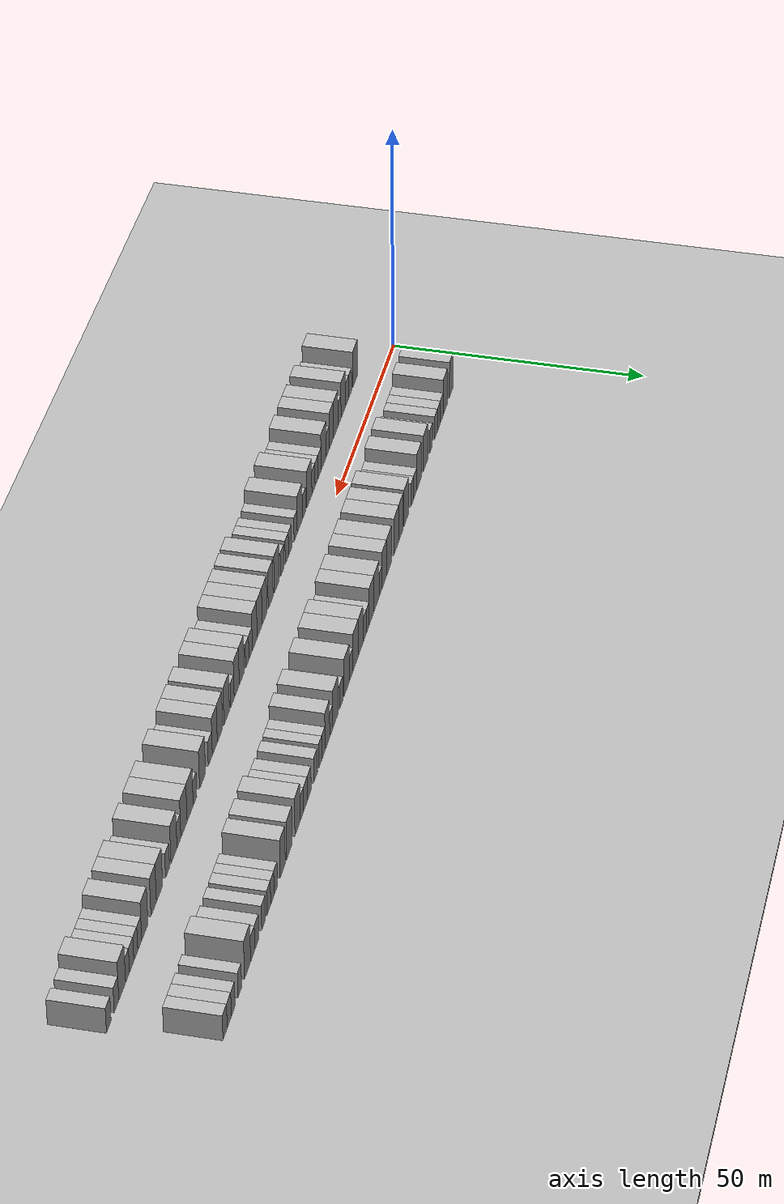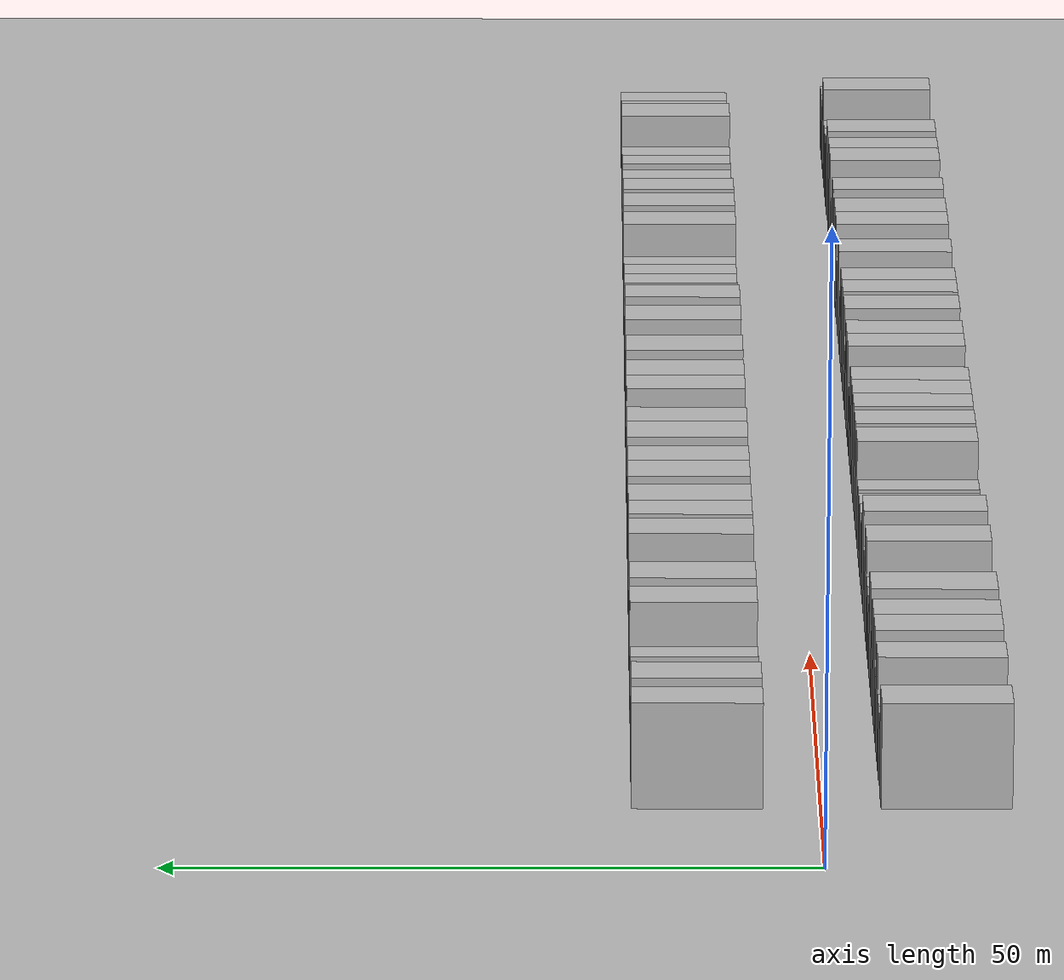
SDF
<?xml version="1.0" encoding="utf-8"?>

<sdf version="1.6">

   <world name="default">

      <gui fullscreen="0">

         <camera name="user_camera">

            <pose>-15 0 4.57585 0 0 0</pose>

            <view_controller>orbit</view_controller>

         </camera>

      </gui>

      <scene>

         <sky>

           <clouds>

             <speed>12</speed>

           </clouds>

         </sky>

         <ambient>0.4 0.4 0.4 1</ambient>

         <background>0.7 0.7 0.7 1</background>

         <shadows>1</shadows>

      </scene>

      <gravity>0 0 -9.8066</gravity>

      <magnetic_field>6e-06 2.3e-05 -4.2e-05</magnetic_field>

      <physics default="0" name="default_physics" type="ode">

         <ode>

            <solver>

               <type>quick</type>

               <iters>10</iters>

               <sor>1.0</sor>

               <use_dynamic_moi_rescaling>0</use_dynamic_moi_rescaling>

            </solver>

            <constraints>

               <cfm>0</cfm>

               <erp>0.2</erp>

               <contact_max_correcting_vel>100</contact_max_correcting_vel>

               <contact_surface_layer>0.001</contact_surface_layer>

            </constraints>

         </ode>

         <max_step_size>0.004</max_step_size>

         <real_time_factor>1</real_time_factor>

         <real_time_update_rate>250</real_time_update_rate>

      </physics>

      <light name="sun" type="directional">

         <cast_shadows>1</cast_shadows>

         <pose>0 0 10 0 0 0</pose>

         <diffuse>0.8 0.8 0.8 1</diffuse>

         <specular>0.2 0.2 0.2 1</specular>

         <attenuation>

            <range>1000</range>

            <constant>0.9</constant>

            <linear>0.01</linear>

            <quadratic>0.001</quadratic>

         </attenuation>

         <direction>-0.5 0.1 -0.9</direction>

      </light>

      <include>

         <name>ground_plane_1</name>

         <uri>model://HANNAS_ground_plane</uri>

         <pose>0 0 0  0 0 0</pose>

      </include>

      <include>

         <name>ground_plane_2</name>

         <uri>model://HANNAS_ground_plane</uri>

         <pose>100 0 0  0 0 0</pose>

      </include>

      <model name="building_1">

         <static>1</static>

         <pose frame="">13.9104 9.5000 0 0.000000 0.000000 1.570796</pose>

         <link name="link">

            <pose frame="">0 0 4.50 0 0 0</pose>

            <collision name="collision">

               <geometry>

                  <box>

                     <size>10.0000 3.8207 9.0000</size>

                  </box>

               </geometry>

               <max_contacts>10</max_contacts>

               <surface>

                  <contact>

                     <ode/>

                  </contact>

                  <bounce/>

                  <friction>

                     <torsional>

                        <ode/>

                     </torsional>

                     <ode/>

                  </friction>

               </surface>

            </collision>

            <visual name="visual">

               <cast_shadows>0</cast_shadows>

               <geometry>

                  <box>

                     <size>10.0000 3.8207 9.0000</size>

                  </box>

               </geometry>

               <material>

                  <script>

                     <uri>model://HANNAS_wall/materials/scripts</uri>

                     <uri>model://HANNAS_wall/materials/textures</uri>

                     <name>vrc/HANNAS_wall</name>

                  </script>

               </material>

            </visual>

            <self_collide>0</self_collide>

            <enable_wind>0</enable_wind>

            <kinematic>0</kinematic>

         </link>

      </model>

      <model name="building_2">

         <static>1</static>

         <pose frame="">19.7886 9.5000 0 0.000000 0.000000 1.570796</pose>

         <link name="link">

            <pose frame="">0 0 4.50 0 0 0</pose>

            <collision name="collision">

               <geometry>

                  <box>

                     <size>10.0000 3.9357 9.0000</size>

                  </box>

               </geometry>

               <max_contacts>10</max_contacts>

               <surface>

                  <contact>

                     <ode/>

                  </contact>

                  <bounce/>

                  <friction>

                     <torsional>

                        <ode/>

                     </torsional>

                     <ode/>

                  </friction>

               </surface>

            </collision>

            <visual name="visual">

               <cast_shadows>0</cast_shadows>

               <geometry>

                  <box>

                     <size>10.0000 3.9357 9.0000</size>

                  </box>

               </geometry>

               <material>

                  <script>

                     <uri>model://HANNAS_wall/materials/scripts</uri>

                     <uri>model://HANNAS_wall/materials/textures</uri>

                     <name>vrc/HANNAS_wall</name>

                  </script>

               </material>

            </visual>

            <self_collide>0</self_collide>

            <enable_wind>0</enable_wind>

            <kinematic>0</kinematic>

         </link>

      </model>

      <model name="building_3">

         <static>1</static>

         <pose frame="">23.0995 9.5000 0 0.000000 0.000000 1.570796</pose>

         <link name="link">

            <pose frame="">0 0 3.00 0 0 0</pose>

            <collision name="collision">

               <geometry>

                  <box>

                     <size>10.0000 2.6862 6.0000</size>

                  </box>

               </geometry>

               <max_contacts>10</max_contacts>

               <surface>

                  <contact>

                     <ode/>

                  </contact>

                  <bounce/>

                  <friction>

                     <torsional>

                        <ode/>

                     </torsional>

                     <ode/>

                  </friction>

               </surface>

            </collision>

            <visual name="visual">

               <cast_shadows>0</cast_shadows>

               <geometry>

                  <box>

                     <size>10.0000 2.6862 6.0000</size>

                  </box>

               </geometry>

               <material>

                  <script>

                     <uri>model://HANNAS_wall/materials/scripts</uri>

                     <uri>model://HANNAS_wall/materials/textures</uri>

                     <name>vrc/HANNAS_wall</name>

                  </script>

               </material>

            </visual>

            <self_collide>0</self_collide>

            <enable_wind>0</enable_wind>

            <kinematic>0</kinematic>

         </link>

      </model>

      <model name="building_4">

         <static>1</static>

         <pose frame="">25.7818 9.5000 0 0.000000 0.000000 1.570796</pose>

         <link name="link">

            <pose frame="">0 0 3.00 0 0 0</pose>

            <collision name="collision">

               <geometry>

                  <box>

                     <size>10.0000 2.6783 6.0000</size>

                  </box>

               </geometry>

               <max_contacts>10</max_contacts>

               <surface>

                  <contact>

                     <ode/>

                  </contact>

                  <bounce/>

                  <friction>

                     <torsional>

                        <ode/>

                     </torsional>

                     <ode/>

                  </friction>

               </surface>

            </collision>

            <visual name="visual">

               <cast_shadows>0</cast_shadows>

               <geometry>

                  <box>

                     <size>10.0000 2.6783 6.0000</size>

                  </box>

               </geometry>

               <material>

                  <script>

                     <uri>model://HANNAS_wall/materials/scripts</uri>

                     <uri>model://HANNAS_wall/materials/textures</uri>

                     <name>vrc/HANNAS_wall</name>

                  </script>

               </material>

            </visual>

            <self_collide>0</self_collide>

            <enable_wind>0</enable_wind>

            <kinematic>0</kinematic>

         </link>

      </model>

      <model name="building_5">

         <static>1</static>

         <pose frame="">28.4317 9.5000 0 0.000000 0.000000 1.570796</pose>

         <link name="link">

            <pose frame="">0 0 3.00 0 0 0</pose>

            <collision name="collision">

               <geometry>

                  <box>

                     <size>10.0000 2.6215 6.0000</size>

                  </box>

               </geometry>

               <max_contacts>10</max_contacts>

               <surface>

                  <contact>

                     <ode/>

                  </contact>

                  <bounce/>

                  <friction>

                     <torsional>

                        <ode/>

                     </torsional>

                     <ode/>

                  </friction>

               </surface>

            </collision>

            <visual name="visual">

               <cast_shadows>0</cast_shadows>

               <geometry>

                  <box>

                     <size>10.0000 2.6215 6.0000</size>

                  </box>

               </geometry>

               <material>

                  <script>

                     <uri>model://HANNAS_wall/materials/scripts</uri>

                     <uri>model://HANNAS_wall/materials/textures</uri>

                     <name>vrc/HANNAS_wall</name>

                  </script>

               </material>

            </visual>

            <self_collide>0</self_collide>

            <enable_wind>0</enable_wind>

            <kinematic>0</kinematic>

         </link>

      </model>

      <model name="building_6">

         <static>1</static>

         <pose frame="">32.9485 9.5000 0 0.000000 0.000000 1.570796</pose>

         <link name="link">

            <pose frame="">0 0 3.00 0 0 0</pose>

            <collision name="collision">

               <geometry>

                  <box>

                     <size>10.0000 2.4121 6.0000</size>

                  </box>

               </geometry>

               <max_contacts>10</max_contacts>

               <surface>

                  <contact>

                     <ode/>

                  </contact>

                  <bounce/>

                  <friction>

                     <torsional>

                        <ode/>

                     </torsional>

                     <ode/>

                  </friction>

               </surface>

            </collision>

            <visual name="visual">

               <cast_shadows>0</cast_shadows>

               <geometry>

                  <box>

                     <size>10.0000 2.4121 6.0000</size>

                  </box>

               </geometry>

               <material>

                  <script>

                     <uri>model://HANNAS_wall/materials/scripts</uri>

                     <uri>model://HANNAS_wall/materials/textures</uri>

                     <name>vrc/HANNAS_wall</name>

                  </script>

               </material>

            </visual>

            <self_collide>0</self_collide>

            <enable_wind>0</enable_wind>

            <kinematic>0</kinematic>

         </link>

      </model>

      <model name="building_7">

         <static>1</static>

         <pose frame="">38.1635 9.5000 0 0.000000 0.000000 1.570796</pose>

         <link name="link">

            <pose frame="">0 0 4.50 0 0 0</pose>

            <collision name="collision">

               <geometry>

                  <box>

                     <size>10.0000 4.0180 9.0000</size>

                  </box>

               </geometry>

               <max_contacts>10</max_contacts>

               <surface>

                  <contact>

                     <ode/>

                  </contact>

                  <bounce/>

                  <friction>

                     <torsional>

                        <ode/>

                     </torsional>

                     <ode/>

                  </friction>

               </surface>

            </collision>

            <visual name="visual">

               <cast_shadows>0</cast_shadows>

               <geometry>

                  <box>

                     <size>10.0000 4.0180 9.0000</size>

                  </box>

               </geometry>

               <material>

                  <script>

                     <uri>model://HANNAS_wall/materials/scripts</uri>

                     <uri>model://HANNAS_wall/materials/textures</uri>

                     <name>vrc/HANNAS_wall</name>

                  </script>

               </material>

            </visual>

            <self_collide>0</self_collide>

            <enable_wind>0</enable_wind>

            <kinematic>0</kinematic>

         </link>

      </model>

      <model name="building_8">

         <static>1</static>

         <pose frame="">44.2379 9.5000 0 0.000000 0.000000 1.570796</pose>

         <link name="link">

            <pose frame="">0 0 4.50 0 0 0</pose>

            <collision name="collision">

               <geometry>

                  <box>

                     <size>10.0000 4.1307 9.0000</size>

                  </box>

               </geometry>

               <max_contacts>10</max_contacts>

               <surface>

                  <contact>

                     <ode/>

                  </contact>

                  <bounce/>

                  <friction>

                     <torsional>

                        <ode/>

                     </torsional>

                     <ode/>

                  </friction>

               </surface>

            </collision>

            <visual name="visual">

               <cast_shadows>0</cast_shadows>

               <geometry>

                  <box>

                     <size>10.0000 4.1307 9.0000</size>

                  </box>

               </geometry>

               <material>

                  <script>

                     <uri>model://HANNAS_wall/materials/scripts</uri>

                     <uri>model://HANNAS_wall/materials/textures</uri>

                     <name>vrc/HANNAS_wall</name>

                  </script>

               </material>

            </visual>

            <self_collide>0</self_collide>

            <enable_wind>0</enable_wind>

            <kinematic>0</kinematic>

         </link>

      </model>

      <model name="building_9">

         <static>1</static>

         <pose frame="">47.6634 9.5000 0 0.000000 0.000000 1.570796</pose>

         <link name="link">

            <pose frame="">0 0 3.00 0 0 0</pose>

            <collision name="collision">

               <geometry>

                  <box>

                     <size>10.0000 2.7204 6.0000</size>

                  </box>

               </geometry>

               <max_contacts>10</max_contacts>

               <surface>

                  <contact>

                     <ode/>

                  </contact>

                  <bounce/>

                  <friction>

                     <torsional>

                        <ode/>

                     </torsional>

                     <ode/>

                  </friction>

               </surface>

            </collision>

            <visual name="visual">

               <cast_shadows>0</cast_shadows>

               <geometry>

                  <box>

                     <size>10.0000 2.7204 6.0000</size>

                  </box>

               </geometry>

               <material>

                  <script>

                     <uri>model://HANNAS_wall/materials/scripts</uri>

                     <uri>model://HANNAS_wall/materials/textures</uri>

                     <name>vrc/HANNAS_wall</name>

                  </script>

               </material>

            </visual>

            <self_collide>0</self_collide>

            <enable_wind>0</enable_wind>

            <kinematic>0</kinematic>

         </link>

      </model>

      <model name="building_10">

         <static>1</static>

         <pose frame="">50.2555 9.5000 0 0.000000 0.000000 1.570796</pose>

         <link name="link">

            <pose frame="">0 0 3.00 0 0 0</pose>

            <collision name="collision">

               <geometry>

                  <box>

                     <size>10.0000 2.4636 6.0000</size>

                  </box>

               </geometry>

               <max_contacts>10</max_contacts>

               <surface>

                  <contact>

                     <ode/>

                  </contact>

                  <bounce/>

                  <friction>

                     <torsional>

                        <ode/>

                     </torsional>

                     <ode/>

                  </friction>

               </surface>

            </collision>

            <visual name="visual">

               <cast_shadows>0</cast_shadows>

               <geometry>

                  <box>

                     <size>10.0000 2.4636 6.0000</size>

                  </box>

               </geometry>

               <material>

                  <script>

                     <uri>model://HANNAS_wall/materials/scripts</uri>

                     <uri>model://HANNAS_wall/materials/textures</uri>

                     <name>vrc/HANNAS_wall</name>

                  </script>

               </material>

            </visual>

            <self_collide>0</self_collide>

            <enable_wind>0</enable_wind>

            <kinematic>0</kinematic>

         </link>

      </model>

      <model name="building_11">

         <static>1</static>

         <pose frame="">55.5296 9.5000 0 0.000000 0.000000 1.570796</pose>

         <link name="link">

            <pose frame="">0 0 4.50 0 0 0</pose>

            <collision name="collision">

               <geometry>

                  <box>

                     <size>10.0000 4.0846 9.0000</size>

                  </box>

               </geometry>

               <max_contacts>10</max_contacts>

               <surface>

                  <contact>

                     <ode/>

                  </contact>

                  <bounce/>

                  <friction>

                     <torsional>

                        <ode/>

                     </torsional>

                     <ode/>

                  </friction>

               </surface>

            </collision>

            <visual name="visual">

               <cast_shadows>0</cast_shadows>

               <geometry>

                  <box>

                     <size>10.0000 4.0846 9.0000</size>

                  </box>

               </geometry>

               <material>

                  <script>

                     <uri>model://HANNAS_wall/materials/scripts</uri>

                     <uri>model://HANNAS_wall/materials/textures</uri>

                     <name>vrc/HANNAS_wall</name>

                  </script>

               </material>

            </visual>

            <self_collide>0</self_collide>

            <enable_wind>0</enable_wind>

            <kinematic>0</kinematic>

         </link>

      </model>

      <model name="building_12">

         <static>1</static>

         <pose frame="">60.4304 9.5000 0 0.000000 0.000000 1.570796</pose>

         <link name="link">

            <pose frame="">0 0 4.50 0 0 0</pose>

            <collision name="collision">

               <geometry>

                  <box>

                     <size>10.0000 3.7170 9.0000</size>

                  </box>

               </geometry>

               <max_contacts>10</max_contacts>

               <surface>

                  <contact>

                     <ode/>

                  </contact>

                  <bounce/>

                  <friction>

                     <torsional>

                        <ode/>

                     </torsional>

                     <ode/>

                  </friction>

               </surface>

            </collision>

            <visual name="visual">

               <cast_shadows>0</cast_shadows>

               <geometry>

                  <box>

                     <size>10.0000 3.7170 9.0000</size>

                  </box>

               </geometry>

               <material>

                  <script>

                     <uri>model://HANNAS_wall/materials/scripts</uri>

                     <uri>model://HANNAS_wall/materials/textures</uri>

                     <name>vrc/HANNAS_wall</name>

                  </script>

               </material>

            </visual>

            <self_collide>0</self_collide>

            <enable_wind>0</enable_wind>

            <kinematic>0</kinematic>

         </link>

      </model>

      <model name="building_13">

         <static>1</static>

         <pose frame="">64.4429 9.5000 0 0.000000 0.000000 1.570796</pose>

         <link name="link">

            <pose frame="">0 0 4.50 0 0 0</pose>

            <collision name="collision">

               <geometry>

                  <box>

                     <size>10.0000 4.3080 9.0000</size>

                  </box>

               </geometry>

               <max_contacts>10</max_contacts>

               <surface>

                  <contact>

                     <ode/>

                  </contact>

                  <bounce/>

                  <friction>

                     <torsional>

                        <ode/>

                     </torsional>

                     <ode/>

                  </friction>

               </surface>

            </collision>

            <visual name="visual">

               <cast_shadows>0</cast_shadows>

               <geometry>

                  <box>

                     <size>10.0000 4.3080 9.0000</size>

                  </box>

               </geometry>

               <material>

                  <script>

                     <uri>model://HANNAS_wall/materials/scripts</uri>

                     <uri>model://HANNAS_wall/materials/textures</uri>

                     <name>vrc/HANNAS_wall</name>

                  </script>

               </material>

            </visual>

            <self_collide>0</self_collide>

            <enable_wind>0</enable_wind>

            <kinematic>0</kinematic>

         </link>

      </model>

      <model name="building_14">

         <static>1</static>

         <pose frame="">70.8151 9.5000 0 0.000000 0.000000 1.570796</pose>

         <link name="link">

            <pose frame="">0 0 4.50 0 0 0</pose>

            <collision name="collision">

               <geometry>

                  <box>

                     <size>10.0000 4.4365 9.0000</size>

                  </box>

               </geometry>

               <max_contacts>10</max_contacts>

               <surface>

                  <contact>

                     <ode/>

                  </contact>

                  <bounce/>

                  <friction>

                     <torsional>

                        <ode/>

                     </torsional>

                     <ode/>

                  </friction>

               </surface>

            </collision>

            <visual name="visual">

               <cast_shadows>0</cast_shadows>

               <geometry>

                  <box>

                     <size>10.0000 4.4365 9.0000</size>

                  </box>

               </geometry>

               <material>

                  <script>

                     <uri>model://HANNAS_wall/materials/scripts</uri>

                     <uri>model://HANNAS_wall/materials/textures</uri>

                     <name>vrc/HANNAS_wall</name>

                  </script>

               </material>

            </visual>

            <self_collide>0</self_collide>

            <enable_wind>0</enable_wind>

            <kinematic>0</kinematic>

         </link>

      </model>

      <model name="building_15">

         <static>1</static>

         <pose frame="">74.9589 9.5000 0 0.000000 0.000000 1.570796</pose>

         <link name="link">

            <pose frame="">0 0 4.50 0 0 0</pose>

            <collision name="collision">

               <geometry>

                  <box>

                     <size>10.0000 3.8510 9.0000</size>

                  </box>

               </geometry>

               <max_contacts>10</max_contacts>

               <surface>

                  <contact>

                     <ode/>

                  </contact>

                  <bounce/>

                  <friction>

                     <torsional>

                        <ode/>

                     </torsional>

                     <ode/>

                  </friction>

               </surface>

            </collision>

            <visual name="visual">

               <cast_shadows>0</cast_shadows>

               <geometry>

                  <box>

                     <size>10.0000 3.8510 9.0000</size>

                  </box>

               </geometry>

               <material>

                  <script>

                     <uri>model://HANNAS_wall/materials/scripts</uri>

                     <uri>model://HANNAS_wall/materials/textures</uri>

                     <name>vrc/HANNAS_wall</name>

                  </script>

               </material>

            </visual>

            <self_collide>0</self_collide>

            <enable_wind>0</enable_wind>

            <kinematic>0</kinematic>

         </link>

      </model>

      <model name="building_16">

         <static>1</static>

         <pose frame="">78.1295 9.5000 0 0.000000 0.000000 1.570796</pose>

         <link name="link">

            <pose frame="">0 0 3.00 0 0 0</pose>

            <collision name="collision">

               <geometry>

                  <box>

                     <size>10.0000 2.4902 6.0000</size>

                  </box>

               </geometry>

               <max_contacts>10</max_contacts>

               <surface>

                  <contact>

                     <ode/>

                  </contact>

                  <bounce/>

                  <friction>

                     <torsional>

                        <ode/>

                     </torsional>

                     <ode/>

                  </friction>

               </surface>

            </collision>

            <visual name="visual">

               <cast_shadows>0</cast_shadows>

               <geometry>

                  <box>

                     <size>10.0000 2.4902 6.0000</size>

                  </box>

               </geometry>

               <material>

                  <script>

                     <uri>model://HANNAS_wall/materials/scripts</uri>

                     <uri>model://HANNAS_wall/materials/textures</uri>

                     <name>vrc/HANNAS_wall</name>

                  </script>

               </material>

            </visual>

            <self_collide>0</self_collide>

            <enable_wind>0</enable_wind>

            <kinematic>0</kinematic>

         </link>

      </model>

      <model name="building_17">

         <static>1</static>

         <pose frame="">81.5890 9.5000 0 0.000000 0.000000 1.570796</pose>

         <link name="link">

            <pose frame="">0 0 4.50 0 0 0</pose>

            <collision name="collision">

               <geometry>

                  <box>

                     <size>10.0000 4.4287 9.0000</size>

                  </box>

               </geometry>

               <max_contacts>10</max_contacts>

               <surface>

                  <contact>

                     <ode/>

                  </contact>

                  <bounce/>

                  <friction>

                     <torsional>

                        <ode/>

                     </torsional>

                     <ode/>

                  </friction>

               </surface>

            </collision>

            <visual name="visual">

               <cast_shadows>0</cast_shadows>

               <geometry>

                  <box>

                     <size>10.0000 4.4287 9.0000</size>

                  </box>

               </geometry>

               <material>

                  <script>

                     <uri>model://HANNAS_wall/materials/scripts</uri>

                     <uri>model://HANNAS_wall/materials/textures</uri>

                     <name>vrc/HANNAS_wall</name>

                  </script>

               </material>

            </visual>

            <self_collide>0</self_collide>

            <enable_wind>0</enable_wind>

            <kinematic>0</kinematic>

         </link>

      </model>

      <model name="building_18">

         <static>1</static>

         <pose frame="">85.7717 9.5000 0 0.000000 0.000000 1.570796</pose>

         <link name="link">

            <pose frame="">0 0 4.50 0 0 0</pose>

            <collision name="collision">

               <geometry>

                  <box>

                     <size>10.0000 3.9368 9.0000</size>

                  </box>

               </geometry>

               <max_contacts>10</max_contacts>

               <surface>

                  <contact>

                     <ode/>

                  </contact>

                  <bounce/>

                  <friction>

                     <torsional>

                        <ode/>

                     </torsional>

                     <ode/>

                  </friction>

               </surface>

            </collision>

            <visual name="visual">

               <cast_shadows>0</cast_shadows>

               <geometry>

                  <box>

                     <size>10.0000 3.9368 9.0000</size>

                  </box>

               </geometry>

               <material>

                  <script>

                     <uri>model://HANNAS_wall/materials/scripts</uri>

                     <uri>model://HANNAS_wall/materials/textures</uri>

                     <name>vrc/HANNAS_wall</name>

                  </script>

               </material>

            </visual>

            <self_collide>0</self_collide>

            <enable_wind>0</enable_wind>

            <kinematic>0</kinematic>

         </link>

      </model>

      <model name="building_19">

         <static>1</static>

         <pose frame="">88.9644 9.5000 0 0.000000 0.000000 1.570796</pose>

         <link name="link">

            <pose frame="">0 0 3.00 0 0 0</pose>

            <collision name="collision">

               <geometry>

                  <box>

                     <size>10.0000 2.4485 6.0000</size>

                  </box>

               </geometry>

               <max_contacts>10</max_contacts>

               <surface>

                  <contact>

                     <ode/>

                  </contact>

                  <bounce/>

                  <friction>

                     <torsional>

                        <ode/>

                     </torsional>

                     <ode/>

                  </friction>

               </surface>

            </collision>

            <visual name="visual">

               <cast_shadows>0</cast_shadows>

               <geometry>

                  <box>

                     <size>10.0000 2.4485 6.0000</size>

                  </box>

               </geometry>

               <material>

                  <script>

                     <uri>model://HANNAS_wall/materials/scripts</uri>

                     <uri>model://HANNAS_wall/materials/textures</uri>

                     <name>vrc/HANNAS_wall</name>

                  </script>

               </material>

            </visual>

            <self_collide>0</self_collide>

            <enable_wind>0</enable_wind>

            <kinematic>0</kinematic>

         </link>

      </model>

      <model name="building_20">

         <static>1</static>

         <pose frame="">91.5721 9.5000 0 0.000000 0.000000 1.570796</pose>

         <link name="link">

            <pose frame="">0 0 3.00 0 0 0</pose>

            <collision name="collision">

               <geometry>

                  <box>

                     <size>10.0000 2.7670 6.0000</size>

                  </box>

               </geometry>

               <max_contacts>10</max_contacts>

               <surface>

                  <contact>

                     <ode/>

                  </contact>

                  <bounce/>

                  <friction>

                     <torsional>

                        <ode/>

                     </torsional>

                     <ode/>

                  </friction>

               </surface>

            </collision>

            <visual name="visual">

               <cast_shadows>0</cast_shadows>

               <geometry>

                  <box>

                     <size>10.0000 2.7670 6.0000</size>

                  </box>

               </geometry>

               <material>

                  <script>

                     <uri>model://HANNAS_wall/materials/scripts</uri>

                     <uri>model://HANNAS_wall/materials/textures</uri>

                     <name>vrc/HANNAS_wall</name>

                  </script>

               </material>

            </visual>

            <self_collide>0</self_collide>

            <enable_wind>0</enable_wind>

            <kinematic>0</kinematic>

         </link>

      </model>

      <model name="building_21">

         <static>1</static>

         <pose frame="">94.8880 9.5000 0 0.000000 0.000000 1.570796</pose>

         <link name="link">

            <pose frame="">0 0 4.50 0 0 0</pose>

            <collision name="collision">

               <geometry>

                  <box>

                     <size>10.0000 3.8647 9.0000</size>

                  </box>

               </geometry>

               <max_contacts>10</max_contacts>

               <surface>

                  <contact>

                     <ode/>

                  </contact>

                  <bounce/>

                  <friction>

                     <torsional>

                        <ode/>

                     </torsional>

                     <ode/>

                  </friction>

               </surface>

            </collision>

            <visual name="visual">

               <cast_shadows>0</cast_shadows>

               <geometry>

                  <box>

                     <size>10.0000 3.8647 9.0000</size>

                  </box>

               </geometry>

               <material>

                  <script>

                     <uri>model://HANNAS_wall/materials/scripts</uri>

                     <uri>model://HANNAS_wall/materials/textures</uri>

                     <name>vrc/HANNAS_wall</name>

                  </script>

               </material>

            </visual>

            <self_collide>0</self_collide>

            <enable_wind>0</enable_wind>

            <kinematic>0</kinematic>

         </link>

      </model>

      <model name="building_22">

         <static>1</static>

         <pose frame="">99.0522 9.5000 0 0.000000 0.000000 1.570796</pose>

         <link name="link">

            <pose frame="">0 0 4.50 0 0 0</pose>

            <collision name="collision">

               <geometry>

                  <box>

                     <size>10.0000 4.4638 9.0000</size>

                  </box>

               </geometry>

               <max_contacts>10</max_contacts>

               <surface>

                  <contact>

                     <ode/>

                  </contact>

                  <bounce/>

                  <friction>

                     <torsional>

                        <ode/>

                     </torsional>

                     <ode/>

                  </friction>

               </surface>

            </collision>

            <visual name="visual">

               <cast_shadows>0</cast_shadows>

               <geometry>

                  <box>

                     <size>10.0000 4.4638 9.0000</size>

                  </box>

               </geometry>

               <material>

                  <script>

                     <uri>model://HANNAS_wall/materials/scripts</uri>

                     <uri>model://HANNAS_wall/materials/textures</uri>

                     <name>vrc/HANNAS_wall</name>

                  </script>

               </material>

            </visual>

            <self_collide>0</self_collide>

            <enable_wind>0</enable_wind>

            <kinematic>0</kinematic>

         </link>

      </model>

      <model name="building_23">

         <static>1</static>

         <pose frame="">102.7219 9.5000 0 0.000000 0.000000 1.570796</pose>

         <link name="link">

            <pose frame="">0 0 3.00 0 0 0</pose>

            <collision name="collision">

               <geometry>

                  <box>

                     <size>10.0000 2.8756 6.0000</size>

                  </box>

               </geometry>

               <max_contacts>10</max_contacts>

               <surface>

                  <contact>

                     <ode/>

                  </contact>

                  <bounce/>

                  <friction>

                     <torsional>

                        <ode/>

                     </torsional>

                     <ode/>

                  </friction>

               </surface>

            </collision>

            <visual name="visual">

               <cast_shadows>0</cast_shadows>

               <geometry>

                  <box>

                     <size>10.0000 2.8756 6.0000</size>

                  </box>

               </geometry>

               <material>

                  <script>

                     <uri>model://HANNAS_wall/materials/scripts</uri>

                     <uri>model://HANNAS_wall/materials/textures</uri>

                     <name>vrc/HANNAS_wall</name>

                  </script>

               </material>

            </visual>

            <self_collide>0</self_collide>

            <enable_wind>0</enable_wind>

            <kinematic>0</kinematic>

         </link>

      </model>

      <model name="building_24">

         <static>1</static>

         <pose frame="">106.3289 9.5000 0 0.000000 0.000000 1.570796</pose>

         <link name="link">

            <pose frame="">0 0 4.50 0 0 0</pose>

            <collision name="collision">

               <geometry>

                  <box>

                     <size>10.0000 4.3384 9.0000</size>

                  </box>

               </geometry>

               <max_contacts>10</max_contacts>

               <surface>

                  <contact>

                     <ode/>

                  </contact>

                  <bounce/>

                  <friction>

                     <torsional>

                        <ode/>

                     </torsional>

                     <ode/>

                  </friction>

               </surface>

            </collision>

            <visual name="visual">

               <cast_shadows>0</cast_shadows>

               <geometry>

                  <box>

                     <size>10.0000 4.3384 9.0000</size>

                  </box>

               </geometry>

               <material>

                  <script>

                     <uri>model://HANNAS_wall/materials/scripts</uri>

                     <uri>model://HANNAS_wall/materials/textures</uri>

                     <name>vrc/HANNAS_wall</name>

                  </script>

               </material>

            </visual>

            <self_collide>0</self_collide>

            <enable_wind>0</enable_wind>

            <kinematic>0</kinematic>

         </link>

      </model>

      <model name="building_25">

         <static>1</static>

         <pose frame="">110.8491 9.5000 0 0.000000 0.000000 1.570796</pose>

         <link name="link">

            <pose frame="">0 0 3.00 0 0 0</pose>

            <collision name="collision">

               <geometry>

                  <box>

                     <size>10.0000 2.7020 6.0000</size>

                  </box>

               </geometry>

               <max_contacts>10</max_contacts>

               <surface>

                  <contact>

                     <ode/>

                  </contact>

                  <bounce/>

                  <friction>

                     <torsional>

                        <ode/>

                     </torsional>

                     <ode/>

                  </friction>

               </surface>

            </collision>

            <visual name="visual">

               <cast_shadows>0</cast_shadows>

               <geometry>

                  <box>

                     <size>10.0000 2.7020 6.0000</size>

                  </box>

               </geometry>

               <material>

                  <script>

                     <uri>model://HANNAS_wall/materials/scripts</uri>

                     <uri>model://HANNAS_wall/materials/textures</uri>

                     <name>vrc/HANNAS_wall</name>

                  </script>

               </material>

            </visual>

            <self_collide>0</self_collide>

            <enable_wind>0</enable_wind>

            <kinematic>0</kinematic>

         </link>

      </model>

      <model name="building_26">

         <static>1</static>

         <pose frame="">115.3762 9.5000 0 0.000000 0.000000 1.570796</pose>

         <link name="link">

            <pose frame="">0 0 4.50 0 0 0</pose>

            <collision name="collision">

               <geometry>

                  <box>

                     <size>10.0000 4.3522 9.0000</size>

                  </box>

               </geometry>

               <max_contacts>10</max_contacts>

               <surface>

                  <contact>

                     <ode/>

                  </contact>

                  <bounce/>

                  <friction>

                     <torsional>

                        <ode/>

                     </torsional>

                     <ode/>

                  </friction>

               </surface>

            </collision>

            <visual name="visual">

               <cast_shadows>0</cast_shadows>

               <geometry>

                  <box>

                     <size>10.0000 4.3522 9.0000</size>

                  </box>

               </geometry>

               <material>

                  <script>

                     <uri>model://HANNAS_wall/materials/scripts</uri>

                     <uri>model://HANNAS_wall/materials/textures</uri>

                     <name>vrc/HANNAS_wall</name>

                  </script>

               </material>

            </visual>

            <self_collide>0</self_collide>

            <enable_wind>0</enable_wind>

            <kinematic>0</kinematic>

         </link>

      </model>

      <model name="building_27">

         <static>1</static>

         <pose frame="">118.7818 9.5000 0 0.000000 0.000000 1.570796</pose>

         <link name="link">

            <pose frame="">0 0 3.00 0 0 0</pose>

            <collision name="collision">

               <geometry>

                  <box>

                     <size>10.0000 2.4589 6.0000</size>

                  </box>

               </geometry>

               <max_contacts>10</max_contacts>

               <surface>

                  <contact>

                     <ode/>

                  </contact>

                  <bounce/>

                  <friction>

                     <torsional>

                        <ode/>

                     </torsional>

                     <ode/>

                  </friction>

               </surface>

            </collision>

            <visual name="visual">

               <cast_shadows>0</cast_shadows>

               <geometry>

                  <box>

                     <size>10.0000 2.4589 6.0000</size>

                  </box>

               </geometry>

               <material>

                  <script>

                     <uri>model://HANNAS_wall/materials/scripts</uri>

                     <uri>model://HANNAS_wall/materials/textures</uri>

                     <name>vrc/HANNAS_wall</name>

                  </script>

               </material>

            </visual>

            <self_collide>0</self_collide>

            <enable_wind>0</enable_wind>

            <kinematic>0</kinematic>

         </link>

      </model>

      <model name="building_28">

         <static>1</static>

         <pose frame="">121.8533 9.5000 0 0.000000 0.000000 1.570796</pose>

         <link name="link">

            <pose frame="">0 0 4.50 0 0 0</pose>

            <collision name="collision">

               <geometry>

                  <box>

                     <size>10.0000 3.6843 9.0000</size>

                  </box>

               </geometry>

               <max_contacts>10</max_contacts>

               <surface>

                  <contact>

                     <ode/>

                  </contact>

                  <bounce/>

                  <friction>

                     <torsional>

                        <ode/>

                     </torsional>

                     <ode/>

                  </friction>

               </surface>

            </collision>

            <visual name="visual">

               <cast_shadows>0</cast_shadows>

               <geometry>

                  <box>

                     <size>10.0000 3.6843 9.0000</size>

                  </box>

               </geometry>

               <material>

                  <script>

                     <uri>model://HANNAS_wall/materials/scripts</uri>

                     <uri>model://HANNAS_wall/materials/textures</uri>

                     <name>vrc/HANNAS_wall</name>

                  </script>

               </material>

            </visual>

            <self_collide>0</self_collide>

            <enable_wind>0</enable_wind>

            <kinematic>0</kinematic>

         </link>

      </model>

      <model name="building_29">

         <static>1</static>

         <pose frame="">124.9723 9.5000 0 0.000000 0.000000 1.570796</pose>

         <link name="link">

            <pose frame="">0 0 3.00 0 0 0</pose>

            <collision name="collision">

               <geometry>

                  <box>

                     <size>10.0000 2.5536 6.0000</size>

                  </box>

               </geometry>

               <max_contacts>10</max_contacts>

               <surface>

                  <contact>

                     <ode/>

                  </contact>

                  <bounce/>

                  <friction>

                     <torsional>

                        <ode/>

                     </torsional>

                     <ode/>

                  </friction>

               </surface>

            </collision>

            <visual name="visual">

               <cast_shadows>0</cast_shadows>

               <geometry>

                  <box>

                     <size>10.0000 2.5536 6.0000</size>

                  </box>

               </geometry>

               <material>

                  <script>

                     <uri>model://HANNAS_wall/materials/scripts</uri>

                     <uri>model://HANNAS_wall/materials/textures</uri>

                     <name>vrc/HANNAS_wall</name>

                  </script>

               </material>

            </visual>

            <self_collide>0</self_collide>

            <enable_wind>0</enable_wind>

            <kinematic>0</kinematic>

         </link>

      </model>

      <model name="building_30">

         <static>1</static>

         <pose frame="">127.4599 9.5000 0 0.000000 0.000000 1.570796</pose>

         <link name="link">

            <pose frame="">0 0 3.00 0 0 0</pose>

            <collision name="collision">

               <geometry>

                  <box>

                     <size>10.0000 2.4216 6.0000</size>

                  </box>

               </geometry>

               <max_contacts>10</max_contacts>

               <surface>

                  <contact>

                     <ode/>

                  </contact>

                  <bounce/>

                  <friction>

                     <torsional>

                        <ode/>

                     </torsional>

                     <ode/>

                  </friction>

               </surface>

            </collision>

            <visual name="visual">

               <cast_shadows>0</cast_shadows>

               <geometry>

                  <box>

                     <size>10.0000 2.4216 6.0000</size>

                  </box>

               </geometry>

               <material>

                  <script>

                     <uri>model://HANNAS_wall/materials/scripts</uri>

                     <uri>model://HANNAS_wall/materials/textures</uri>

                     <name>vrc/HANNAS_wall</name>

                  </script>

               </material>

            </visual>

            <self_collide>0</self_collide>

            <enable_wind>0</enable_wind>

            <kinematic>0</kinematic>

         </link>

      </model>

      <model name="building_31">

         <static>1</static>

         <pose frame="">131.1179 9.5000 0 0.000000 0.000000 1.570796</pose>

         <link name="link">

            <pose frame="">0 0 3.00 0 0 0</pose>

            <collision name="collision">

               <geometry>

                  <box>

                     <size>10.0000 2.8943 6.0000</size>

                  </box>

               </geometry>

               <max_contacts>10</max_contacts>

               <surface>

                  <contact>

                     <ode/>

                  </contact>

                  <bounce/>

                  <friction>

                     <torsional>

                        <ode/>

                     </torsional>

                     <ode/>

                  </friction>

               </surface>

            </collision>

            <visual name="visual">

               <cast_shadows>0</cast_shadows>

               <geometry>

                  <box>

                     <size>10.0000 2.8943 6.0000</size>

                  </box>

               </geometry>

               <material>

                  <script>

                     <uri>model://HANNAS_wall/materials/scripts</uri>

                     <uri>model://HANNAS_wall/materials/textures</uri>

                     <name>vrc/HANNAS_wall</name>

                  </script>

               </material>

            </visual>

            <self_collide>0</self_collide>

            <enable_wind>0</enable_wind>

            <kinematic>0</kinematic>

         </link>

      </model>

      <model name="building_32">

         <static>1</static>

         <pose frame="">136.0342 9.5000 0 0.000000 0.000000 1.570796</pose>

         <link name="link">

            <pose frame="">0 0 3.00 0 0 0</pose>

            <collision name="collision">

               <geometry>

                  <box>

                     <size>10.0000 2.9383 6.0000</size>

                  </box>

               </geometry>

               <max_contacts>10</max_contacts>

               <surface>

                  <contact>

                     <ode/>

                  </contact>

                  <bounce/>

                  <friction>

                     <torsional>

                        <ode/>

                     </torsional>

                     <ode/>

                  </friction>

               </surface>

            </collision>

            <visual name="visual">

               <cast_shadows>0</cast_shadows>

               <geometry>

                  <box>

                     <size>10.0000 2.9383 6.0000</size>

                  </box>

               </geometry>

               <material>

                  <script>

                     <uri>model://HANNAS_wall/materials/scripts</uri>

                     <uri>model://HANNAS_wall/materials/textures</uri>

                     <name>vrc/HANNAS_wall</name>

                  </script>

               </material>

            </visual>

            <self_collide>0</self_collide>

            <enable_wind>0</enable_wind>

            <kinematic>0</kinematic>

         </link>

      </model>

      <model name="building_33">

         <static>1</static>

         <pose frame="">138.9468 9.5000 0 0.000000 0.000000 1.570796</pose>

         <link name="link">

            <pose frame="">0 0 3.00 0 0 0</pose>

            <collision name="collision">

               <geometry>

                  <box>

                     <size>10.0000 2.8870 6.0000</size>

                  </box>

               </geometry>

               <max_contacts>10</max_contacts>

               <surface>

                  <contact>

                     <ode/>

                  </contact>

                  <bounce/>

                  <friction>

                     <torsional>

                        <ode/>

                     </torsional>

                     <ode/>

                  </friction>

               </surface>

            </collision>

            <visual name="visual">

               <cast_shadows>0</cast_shadows>

               <geometry>

                  <box>

                     <size>10.0000 2.8870 6.0000</size>

                  </box>

               </geometry>

               <material>

                  <script>

                     <uri>model://HANNAS_wall/materials/scripts</uri>

                     <uri>model://HANNAS_wall/materials/textures</uri>

                     <name>vrc/HANNAS_wall</name>

                  </script>

               </material>

            </visual>

            <self_collide>0</self_collide>

            <enable_wind>0</enable_wind>

            <kinematic>0</kinematic>

         </link>

      </model>

      <model name="building_34">

         <static>1</static>

         <pose frame="">141.6442 9.5000 0 0.000000 0.000000 1.570796</pose>

         <link name="link">

            <pose frame="">0 0 3.00 0 0 0</pose>

            <collision name="collision">

               <geometry>

                  <box>

                     <size>10.0000 2.5078 6.0000</size>

                  </box>

               </geometry>

               <max_contacts>10</max_contacts>

               <surface>

                  <contact>

                     <ode/>

                  </contact>

                  <bounce/>

                  <friction>

                     <torsional>

                        <ode/>

                     </torsional>

                     <ode/>

                  </friction>

               </surface>

            </collision>

            <visual name="visual">

               <cast_shadows>0</cast_shadows>

               <geometry>

                  <box>

                     <size>10.0000 2.5078 6.0000</size>

                  </box>

               </geometry>

               <material>

                  <script>

                     <uri>model://HANNAS_wall/materials/scripts</uri>

                     <uri>model://HANNAS_wall/materials/textures</uri>

                     <name>vrc/HANNAS_wall</name>

                  </script>

               </material>

            </visual>

            <self_collide>0</self_collide>

            <enable_wind>0</enable_wind>

            <kinematic>0</kinematic>

         </link>

      </model>

      <model name="building_35">

         <static>1</static>

         <pose frame="">144.9210 9.5000 0 0.000000 0.000000 1.570796</pose>

         <link name="link">

            <pose frame="">0 0 4.50 0 0 0</pose>

            <collision name="collision">

               <geometry>

                  <box>

                     <size>10.0000 4.0458 9.0000</size>

                  </box>

               </geometry>

               <max_contacts>10</max_contacts>

               <surface>

                  <contact>

                     <ode/>

                  </contact>

                  <bounce/>

                  <friction>

                     <torsional>

                        <ode/>

                     </torsional>

                     <ode/>

                  </friction>

               </surface>

            </collision>

            <visual name="visual">

               <cast_shadows>0</cast_shadows>

               <geometry>

                  <box>

                     <size>10.0000 4.0458 9.0000</size>

                  </box>

               </geometry>

               <material>

                  <script>

                     <uri>model://HANNAS_wall/materials/scripts</uri>

                     <uri>model://HANNAS_wall/materials/textures</uri>

                     <name>vrc/HANNAS_wall</name>

                  </script>

               </material>

            </visual>

            <self_collide>0</self_collide>

            <enable_wind>0</enable_wind>

            <kinematic>0</kinematic>

         </link>

      </model>

      <model name="building_36">

         <static>1</static>

         <pose frame="">151.0534 9.5000 0 0.000000 0.000000 1.570796</pose>

         <link name="link">

            <pose frame="">0 0 4.50 0 0 0</pose>

            <collision name="collision">

               <geometry>

                  <box>

                     <size>10.0000 4.2190 9.0000</size>

                  </box>

               </geometry>

               <max_contacts>10</max_contacts>

               <surface>

                  <contact>

                     <ode/>

                  </contact>

                  <bounce/>

                  <friction>

                     <torsional>

                        <ode/>

                     </torsional>

                     <ode/>

                  </friction>

               </surface>

            </collision>

            <visual name="visual">

               <cast_shadows>0</cast_shadows>

               <geometry>

                  <box>

                     <size>10.0000 4.2190 9.0000</size>

                  </box>

               </geometry>

               <material>

                  <script>

                     <uri>model://HANNAS_wall/materials/scripts</uri>

                     <uri>model://HANNAS_wall/materials/textures</uri>

                     <name>vrc/HANNAS_wall</name>

                  </script>

               </material>

            </visual>

            <self_collide>0</self_collide>

            <enable_wind>0</enable_wind>

            <kinematic>0</kinematic>

         </link>

      </model>

      <model name="building_37">

         <static>1</static>

         <pose frame="">156.0537 9.5000 0 0.000000 0.000000 1.570796</pose>

         <link name="link">

            <pose frame="">0 0 4.50 0 0 0</pose>

            <collision name="collision">

               <geometry>

                  <box>

                     <size>10.0000 3.7815 9.0000</size>

                  </box>

               </geometry>

               <max_contacts>10</max_contacts>

               <surface>

                  <contact>

                     <ode/>

                  </contact>

                  <bounce/>

                  <friction>

                     <torsional>

                        <ode/>

                     </torsional>

                     <ode/>

                  </friction>

               </surface>

            </collision>

            <visual name="visual">

               <cast_shadows>0</cast_shadows>

               <geometry>

                  <box>

                     <size>10.0000 3.7815 9.0000</size>

                  </box>

               </geometry>

               <material>

                  <script>

                     <uri>model://HANNAS_wall/materials/scripts</uri>

                     <uri>model://HANNAS_wall/materials/textures</uri>

                     <name>vrc/HANNAS_wall</name>

                  </script>

               </material>

            </visual>

            <self_collide>0</self_collide>

            <enable_wind>0</enable_wind>

            <kinematic>0</kinematic>

         </link>

      </model>

      <model name="building_38">

         <static>1</static>

         <pose frame="">161.1519 9.5000 0 0.000000 0.000000 1.570796</pose>

         <link name="link">

            <pose frame="">0 0 3.00 0 0 0</pose>

            <collision name="collision">

               <geometry>

                  <box>

                     <size>10.0000 2.4148 6.0000</size>

                  </box>

               </geometry>

               <max_contacts>10</max_contacts>

               <surface>

                  <contact>

                     <ode/>

                  </contact>

                  <bounce/>

                  <friction>

                     <torsional>

                        <ode/>

                     </torsional>

                     <ode/>

                  </friction>

               </surface>

            </collision>

            <visual name="visual">

               <cast_shadows>0</cast_shadows>

               <geometry>

                  <box>

                     <size>10.0000 2.4148 6.0000</size>

                  </box>

               </geometry>

               <material>

                  <script>

                     <uri>model://HANNAS_wall/materials/scripts</uri>

                     <uri>model://HANNAS_wall/materials/textures</uri>

                     <name>vrc/HANNAS_wall</name>

                  </script>

               </material>

            </visual>

            <self_collide>0</self_collide>

            <enable_wind>0</enable_wind>

            <kinematic>0</kinematic>

         </link>

      </model>

      <model name="building_39">

         <static>1</static>

         <pose frame="">163.5922 9.5000 0 0.000000 0.000000 1.570796</pose>

         <link name="link">

            <pose frame="">0 0 3.00 0 0 0</pose>

            <collision name="collision">

               <geometry>

                  <box>

                     <size>10.0000 2.4658 6.0000</size>

                  </box>

               </geometry>

               <max_contacts>10</max_contacts>

               <surface>

                  <contact>

                     <ode/>

                  </contact>

                  <bounce/>

                  <friction>

                     <torsional>

                        <ode/>

                     </torsional>

                     <ode/>

                  </friction>

               </surface>

            </collision>

            <visual name="visual">

               <cast_shadows>0</cast_shadows>

               <geometry>

                  <box>

                     <size>10.0000 2.4658 6.0000</size>

                  </box>

               </geometry>

               <material>

                  <script>

                     <uri>model://HANNAS_wall/materials/scripts</uri>

                     <uri>model://HANNAS_wall/materials/textures</uri>

                     <name>vrc/HANNAS_wall</name>

                  </script>

               </material>

            </visual>

            <self_collide>0</self_collide>

            <enable_wind>0</enable_wind>

            <kinematic>0</kinematic>

         </link>

      </model>

      <model name="building_40">

         <static>1</static>

         <pose frame="">166.2034 9.5000 0 0.000000 0.000000 1.570796</pose>

         <link name="link">

            <pose frame="">0 0 3.00 0 0 0</pose>

            <collision name="collision">

               <geometry>

                  <box>

                     <size>10.0000 2.7566 6.0000</size>

                  </box>

               </geometry>

               <max_contacts>10</max_contacts>

               <surface>

                  <contact>

                     <ode/>

                  </contact>

                  <bounce/>

                  <friction>

                     <torsional>

                        <ode/>

                     </torsional>

                     <ode/>

                  </friction>

               </surface>

            </collision>

            <visual name="visual">

               <cast_shadows>0</cast_shadows>

               <geometry>

                  <box>

                     <size>10.0000 2.7566 6.0000</size>

                  </box>

               </geometry>

               <material>

                  <script>

                     <uri>model://HANNAS_wall/materials/scripts</uri>

                     <uri>model://HANNAS_wall/materials/textures</uri>

                     <name>vrc/HANNAS_wall</name>

                  </script>

               </material>

            </visual>

            <self_collide>0</self_collide>

            <enable_wind>0</enable_wind>

            <kinematic>0</kinematic>

         </link>

      </model>

      <model name="building_41">

         <static>1</static>

         <pose frame="">169.9763 9.5000 0 0.000000 0.000000 1.570796</pose>

         <link name="link">

            <pose frame="">0 0 3.00 0 0 0</pose>

            <collision name="collision">

               <geometry>

                  <box>

                     <size>10.0000 2.7892 6.0000</size>

                  </box>

               </geometry>

               <max_contacts>10</max_contacts>

               <surface>

                  <contact>

                     <ode/>

                  </contact>

                  <bounce/>

                  <friction>

                     <torsional>

                        <ode/>

                     </torsional>

                     <ode/>

                  </friction>

               </surface>

            </collision>

            <visual name="visual">

               <cast_shadows>0</cast_shadows>

               <geometry>

                  <box>

                     <size>10.0000 2.7892 6.0000</size>

                  </box>

               </geometry>

               <material>

                  <script>

                     <uri>model://HANNAS_wall/materials/scripts</uri>

                     <uri>model://HANNAS_wall/materials/textures</uri>

                     <name>vrc/HANNAS_wall</name>

                  </script>

               </material>

            </visual>

            <self_collide>0</self_collide>

            <enable_wind>0</enable_wind>

            <kinematic>0</kinematic>

         </link>

      </model>

      <model name="building_42">

         <static>1</static>

         <pose frame="">174.8296 9.5000 0 0.000000 0.000000 1.570796</pose>

         <link name="link">

            <pose frame="">0 0 3.00 0 0 0</pose>

            <collision name="collision">

               <geometry>

                  <box>

                     <size>10.0000 2.9173 6.0000</size>

                  </box>

               </geometry>

               <max_contacts>10</max_contacts>

               <surface>

                  <contact>

                     <ode/>

                  </contact>

                  <bounce/>

                  <friction>

                     <torsional>

                        <ode/>

                     </torsional>

                     <ode/>

                  </friction>

               </surface>

            </collision>

            <visual name="visual">

               <cast_shadows>0</cast_shadows>

               <geometry>

                  <box>

                     <size>10.0000 2.9173 6.0000</size>

                  </box>

               </geometry>

               <material>

                  <script>

                     <uri>model://HANNAS_wall/materials/scripts</uri>

                     <uri>model://HANNAS_wall/materials/textures</uri>

                     <name>vrc/HANNAS_wall</name>

                  </script>

               </material>

            </visual>

            <self_collide>0</self_collide>

            <enable_wind>0</enable_wind>

            <kinematic>0</kinematic>

         </link>

      </model>

      <model name="building_43">

         <static>1</static>

         <pose frame="">177.7691 9.5000 0 0.000000 0.000000 1.570796</pose>

         <link name="link">

            <pose frame="">0 0 3.00 0 0 0</pose>

            <collision name="collision">

               <geometry>

                  <box>

                     <size>10.0000 2.9616 6.0000</size>

                  </box>

               </geometry>

               <max_contacts>10</max_contacts>

               <surface>

                  <contact>

                     <ode/>

                  </contact>

                  <bounce/>

                  <friction>

                     <torsional>

                        <ode/>

                     </torsional>

                     <ode/>

                  </friction>

               </surface>

            </collision>

            <visual name="visual">

               <cast_shadows>0</cast_shadows>

               <geometry>

                  <box>

                     <size>10.0000 2.9616 6.0000</size>

                  </box>

               </geometry>

               <material>

                  <script>

                     <uri>model://HANNAS_wall/materials/scripts</uri>

                     <uri>model://HANNAS_wall/materials/textures</uri>

                     <name>vrc/HANNAS_wall</name>

                  </script>

               </material>

            </visual>

            <self_collide>0</self_collide>

            <enable_wind>0</enable_wind>

            <kinematic>0</kinematic>

         </link>

      </model>

      <model name="building_44">

         <static>1</static>

         <pose frame="">181.4074 9.5000 0 0.000000 0.000000 1.570796</pose>

         <link name="link">

            <pose frame="">0 0 4.50 0 0 0</pose>

            <collision name="collision">

               <geometry>

                  <box>

                     <size>10.0000 4.3151 9.0000</size>

                  </box>

               </geometry>

               <max_contacts>10</max_contacts>

               <surface>

                  <contact>

                     <ode/>

                  </contact>

                  <bounce/>

                  <friction>

                     <torsional>

                        <ode/>

                     </torsional>

                     <ode/>

                  </friction>

               </surface>

            </collision>

            <visual name="visual">

               <cast_shadows>0</cast_shadows>

               <geometry>

                  <box>

                     <size>10.0000 4.3151 9.0000</size>

                  </box>

               </geometry>

               <material>

                  <script>

                     <uri>model://HANNAS_wall/materials/scripts</uri>

                     <uri>model://HANNAS_wall/materials/textures</uri>

                     <name>vrc/HANNAS_wall</name>

                  </script>

               </material>

            </visual>

            <self_collide>0</self_collide>

            <enable_wind>0</enable_wind>

            <kinematic>0</kinematic>

         </link>

      </model>

      <model name="building_45">

         <static>1</static>

         <pose frame="">186.8320 9.5000 0 0.000000 0.000000 1.570796</pose>

         <link name="link">

            <pose frame="">0 0 3.00 0 0 0</pose>

            <collision name="collision">

               <geometry>

                  <box>

                     <size>10.0000 2.5339 6.0000</size>

                  </box>

               </geometry>

               <max_contacts>10</max_contacts>

               <surface>

                  <contact>

                     <ode/>

                  </contact>

                  <bounce/>

                  <friction>

                     <torsional>

                        <ode/>

                     </torsional>

                     <ode/>

                  </friction>

               </surface>

            </collision>

            <visual name="visual">

               <cast_shadows>0</cast_shadows>

               <geometry>

                  <box>

                     <size>10.0000 2.5339 6.0000</size>

                  </box>

               </geometry>

               <material>

                  <script>

                     <uri>model://HANNAS_wall/materials/scripts</uri>

                     <uri>model://HANNAS_wall/materials/textures</uri>

                     <name>vrc/HANNAS_wall</name>

                  </script>

               </material>

            </visual>

            <self_collide>0</self_collide>

            <enable_wind>0</enable_wind>

            <kinematic>0</kinematic>

         </link>

      </model>

      <model name="building_46">

         <static>1</static>

         <pose frame="">191.3920 9.5000 0 0.000000 0.000000 1.570796</pose>

         <link name="link">

            <pose frame="">0 0 3.00 0 0 0</pose>

            <collision name="collision">

               <geometry>

                  <box>

                     <size>10.0000 2.5862 6.0000</size>

                  </box>

               </geometry>

               <max_contacts>10</max_contacts>

               <surface>

                  <contact>

                     <ode/>

                  </contact>

                  <bounce/>

                  <friction>

                     <torsional>

                        <ode/>

                     </torsional>

                     <ode/>

                  </friction>

               </surface>

            </collision>

            <visual name="visual">

               <cast_shadows>0</cast_shadows>

               <geometry>

                  <box>

                     <size>10.0000 2.5862 6.0000</size>

                  </box>

               </geometry>

               <material>

                  <script>

                     <uri>model://HANNAS_wall/materials/scripts</uri>

                     <uri>model://HANNAS_wall/materials/textures</uri>

                     <name>vrc/HANNAS_wall</name>

                  </script>

               </material>

            </visual>

            <self_collide>0</self_collide>

            <enable_wind>0</enable_wind>

            <kinematic>0</kinematic>

         </link>

      </model>

      <model name="building_47">

         <static>1</static>

         <pose frame="">194.1227 9.5000 0 0.000000 0.000000 1.570796</pose>

         <link name="link">

            <pose frame="">0 0 3.00 0 0 0</pose>

            <collision name="collision">

               <geometry>

                  <box>

                     <size>10.0000 2.8751 6.0000</size>

                  </box>

               </geometry>

               <max_contacts>10</max_contacts>

               <surface>

                  <contact>

                     <ode/>

                  </contact>

                  <bounce/>

                  <friction>

                     <torsional>

                        <ode/>

                     </torsional>

                     <ode/>

                  </friction>

               </surface>

            </collision>

            <visual name="visual">

               <cast_shadows>0</cast_shadows>

               <geometry>

                  <box>

                     <size>10.0000 2.8751 6.0000</size>

                  </box>

               </geometry>

               <material>

                  <script>

                     <uri>model://HANNAS_wall/materials/scripts</uri>

                     <uri>model://HANNAS_wall/materials/textures</uri>

                     <name>vrc/HANNAS_wall</name>

                  </script>

               </material>

            </visual>

            <self_collide>0</self_collide>

            <enable_wind>0</enable_wind>

            <kinematic>0</kinematic>

         </link>

      </model>

      <model name="building_48">

         <static>1</static>

         <pose frame="">196.9882 9.5000 0 0.000000 0.000000 1.570796</pose>

         <link name="link">

            <pose frame="">0 0 3.00 0 0 0</pose>

            <collision name="collision">

               <geometry>

                  <box>

                     <size>10.0000 2.8558 6.0000</size>

                  </box>

               </geometry>

               <max_contacts>10</max_contacts>

               <surface>

                  <contact>

                     <ode/>

                  </contact>

                  <bounce/>

                  <friction>

                     <torsional>

                        <ode/>

                     </torsional>

                     <ode/>

                  </friction>

               </surface>

            </collision>

            <visual name="visual">

               <cast_shadows>0</cast_shadows>

               <geometry>

                  <box>

                     <size>10.0000 2.8558 6.0000</size>

                  </box>

               </geometry>

               <material>

                  <script>

                     <uri>model://HANNAS_wall/materials/scripts</uri>

                     <uri>model://HANNAS_wall/materials/textures</uri>

                     <name>vrc/HANNAS_wall</name>

                  </script>

               </material>

            </visual>

            <self_collide>0</self_collide>

            <enable_wind>0</enable_wind>

            <kinematic>0</kinematic>

         </link>

      </model>

      <model name="building_49">

         <static>1</static>

         <pose frame="">14.2105 -9.5000 0 0.000000 0.000000 1.570796</pose>

         <link name="link">

            <pose frame="">0 0 4.50 0 0 0</pose>

            <collision name="collision">

               <geometry>

                  <box>

                     <size>10.0000 4.4210 9.0000</size>

                  </box>

               </geometry>

               <max_contacts>10</max_contacts>

               <surface>

                  <contact>

                     <ode/>

                  </contact>

                  <bounce/>

                  <friction>

                     <torsional>

                        <ode/>

                     </torsional>

                     <ode/>

                  </friction>

               </surface>

            </collision>

            <visual name="visual">

               <cast_shadows>0</cast_shadows>

               <geometry>

                  <box>

                     <size>10.0000 4.4210 9.0000</size>

                  </box>

               </geometry>

               <material>

                  <script>

                     <uri>model://HANNAS_wall/materials/scripts</uri>

                     <uri>model://HANNAS_wall/materials/textures</uri>

                     <name>vrc/HANNAS_wall</name>

                  </script>

               </material>

            </visual>

            <self_collide>0</self_collide>

            <enable_wind>0</enable_wind>

            <kinematic>0</kinematic>

         </link>

      </model>

      <model name="building_50">

         <static>1</static>

         <pose frame="">18.6855 -9.5000 0 0.000000 0.000000 1.570796</pose>

         <link name="link">

            <pose frame="">0 0 3.00 0 0 0</pose>

            <collision name="collision">

               <geometry>

                  <box>

                     <size>10.0000 2.5291 6.0000</size>

                  </box>

               </geometry>

               <max_contacts>10</max_contacts>

               <surface>

                  <contact>

                     <ode/>

                  </contact>

                  <bounce/>

                  <friction>

                     <torsional>

                        <ode/>

                     </torsional>

                     <ode/>

                  </friction>

               </surface>

            </collision>

            <visual name="visual">

               <cast_shadows>0</cast_shadows>

               <geometry>

                  <box>

                     <size>10.0000 2.5291 6.0000</size>

                  </box>

               </geometry>

               <material>

                  <script>

                     <uri>model://HANNAS_wall/materials/scripts</uri>

                     <uri>model://HANNAS_wall/materials/textures</uri>

                     <name>vrc/HANNAS_wall</name>

                  </script>

               </material>

            </visual>

            <self_collide>0</self_collide>

            <enable_wind>0</enable_wind>

            <kinematic>0</kinematic>

         </link>

      </model>

      <model name="building_51">

         <static>1</static>

         <pose frame="">21.4126 -9.5000 0 0.000000 0.000000 1.570796</pose>

         <link name="link">

            <pose frame="">0 0 3.00 0 0 0</pose>

            <collision name="collision">

               <geometry>

                  <box>

                     <size>10.0000 2.9251 6.0000</size>

                  </box>

               </geometry>

               <max_contacts>10</max_contacts>

               <surface>

                  <contact>

                     <ode/>

                  </contact>

                  <bounce/>

                  <friction>

                     <torsional>

                        <ode/>

                     </torsional>

                     <ode/>

                  </friction>

               </surface>

            </collision>

            <visual name="visual">

               <cast_shadows>0</cast_shadows>

               <geometry>

                  <box>

                     <size>10.0000 2.9251 6.0000</size>

                  </box>

               </geometry>

               <material>

                  <script>

                     <uri>model://HANNAS_wall/materials/scripts</uri>

                     <uri>model://HANNAS_wall/materials/textures</uri>

                     <name>vrc/HANNAS_wall</name>

                  </script>

               </material>

            </visual>

            <self_collide>0</self_collide>

            <enable_wind>0</enable_wind>

            <kinematic>0</kinematic>

         </link>

      </model>

      <model name="building_52">

         <static>1</static>

         <pose frame="">24.7919 -9.5000 0 0.000000 0.000000 1.570796</pose>

         <link name="link">

            <pose frame="">0 0 4.50 0 0 0</pose>

            <collision name="collision">

               <geometry>

                  <box>

                     <size>10.0000 3.8335 9.0000</size>

                  </box>

               </geometry>

               <max_contacts>10</max_contacts>

               <surface>

                  <contact>

                     <ode/>

                  </contact>

                  <bounce/>

                  <friction>

                     <torsional>

                        <ode/>

                     </torsional>

                     <ode/>

                  </friction>

               </surface>

            </collision>

            <visual name="visual">

               <cast_shadows>0</cast_shadows>

               <geometry>

                  <box>

                     <size>10.0000 3.8335 9.0000</size>

                  </box>

               </geometry>

               <material>

                  <script>

                     <uri>model://HANNAS_wall/materials/scripts</uri>

                     <uri>model://HANNAS_wall/materials/textures</uri>

                     <name>vrc/HANNAS_wall</name>

                  </script>

               </material>

            </visual>

            <self_collide>0</self_collide>

            <enable_wind>0</enable_wind>

            <kinematic>0</kinematic>

         </link>

      </model>

      <model name="building_53">

         <static>1</static>

         <pose frame="">28.0637 -9.5000 0 0.000000 0.000000 1.570796</pose>

         <link name="link">

            <pose frame="">0 0 3.00 0 0 0</pose>

            <collision name="collision">

               <geometry>

                  <box>

                     <size>10.0000 2.7101 6.0000</size>

                  </box>

               </geometry>

               <max_contacts>10</max_contacts>

               <surface>

                  <contact>

                     <ode/>

                  </contact>

                  <bounce/>

                  <friction>

                     <torsional>

                        <ode/>

                     </torsional>

                     <ode/>

                  </friction>

               </surface>

            </collision>

            <visual name="visual">

               <cast_shadows>0</cast_shadows>

               <geometry>

                  <box>

                     <size>10.0000 2.7101 6.0000</size>

                  </box>

               </geometry>

               <material>

                  <script>

                     <uri>model://HANNAS_wall/materials/scripts</uri>

                     <uri>model://HANNAS_wall/materials/textures</uri>

                     <name>vrc/HANNAS_wall</name>

                  </script>

               </material>

            </visual>

            <self_collide>0</self_collide>

            <enable_wind>0</enable_wind>

            <kinematic>0</kinematic>

         </link>

      </model>

      <model name="building_54">

         <static>1</static>

         <pose frame="">31.3516 -9.5000 0 0.000000 0.000000 1.570796</pose>

         <link name="link">

            <pose frame="">0 0 4.50 0 0 0</pose>

            <collision name="collision">

               <geometry>

                  <box>

                     <size>10.0000 3.8658 9.0000</size>

                  </box>

               </geometry>

               <max_contacts>10</max_contacts>

               <surface>

                  <contact>

                     <ode/>

                  </contact>

                  <bounce/>

                  <friction>

                     <torsional>

                        <ode/>

                     </torsional>

                     <ode/>

                  </friction>

               </surface>

            </collision>

            <visual name="visual">

               <cast_shadows>0</cast_shadows>

               <geometry>

                  <box>

                     <size>10.0000 3.8658 9.0000</size>

                  </box>

               </geometry>

               <material>

                  <script>

                     <uri>model://HANNAS_wall/materials/scripts</uri>

                     <uri>model://HANNAS_wall/materials/textures</uri>

                     <name>vrc/HANNAS_wall</name>

                  </script>

               </material>

            </visual>

            <self_collide>0</self_collide>

            <enable_wind>0</enable_wind>

            <kinematic>0</kinematic>

         </link>

      </model>

      <model name="building_55">

         <static>1</static>

         <pose frame="">35.1412 -9.5000 0 0.000000 0.000000 1.570796</pose>

         <link name="link">

            <pose frame="">0 0 4.50 0 0 0</pose>

            <collision name="collision">

               <geometry>

                  <box>

                     <size>10.0000 3.7134 9.0000</size>

                  </box>

               </geometry>

               <max_contacts>10</max_contacts>

               <surface>

                  <contact>

                     <ode/>

                  </contact>

                  <bounce/>

                  <friction>

                     <torsional>

                        <ode/>

                     </torsional>

                     <ode/>

                  </friction>

               </surface>

            </collision>

            <visual name="visual">

               <cast_shadows>0</cast_shadows>

               <geometry>

                  <box>

                     <size>10.0000 3.7134 9.0000</size>

                  </box>

               </geometry>

               <material>

                  <script>

                     <uri>model://HANNAS_wall/materials/scripts</uri>

                     <uri>model://HANNAS_wall/materials/textures</uri>

                     <name>vrc/HANNAS_wall</name>

                  </script>

               </material>

            </visual>

            <self_collide>0</self_collide>

            <enable_wind>0</enable_wind>

            <kinematic>0</kinematic>

         </link>

      </model>

      <model name="building_56">

         <static>1</static>

         <pose frame="">38.2589 -9.5000 0 0.000000 0.000000 1.570796</pose>

         <link name="link">

            <pose frame="">0 0 3.00 0 0 0</pose>

            <collision name="collision">

               <geometry>

                  <box>

                     <size>10.0000 2.5218 6.0000</size>

                  </box>

               </geometry>

               <max_contacts>10</max_contacts>

               <surface>

                  <contact>

                     <ode/>

                  </contact>

                  <bounce/>

                  <friction>

                     <torsional>

                        <ode/>

                     </torsional>

                     <ode/>

                  </friction>

               </surface>

            </collision>

            <visual name="visual">

               <cast_shadows>0</cast_shadows>

               <geometry>

                  <box>

                     <size>10.0000 2.5218 6.0000</size>

                  </box>

               </geometry>

               <material>

                  <script>

                     <uri>model://HANNAS_wall/materials/scripts</uri>

                     <uri>model://HANNAS_wall/materials/textures</uri>

                     <name>vrc/HANNAS_wall</name>

                  </script>

               </material>

            </visual>

            <self_collide>0</self_collide>

            <enable_wind>0</enable_wind>

            <kinematic>0</kinematic>

         </link>

      </model>

      <model name="building_57">

         <static>1</static>

         <pose frame="">41.7193 -9.5000 0 0.000000 0.000000 1.570796</pose>

         <link name="link">

            <pose frame="">0 0 4.50 0 0 0</pose>

            <collision name="collision">

               <geometry>

                  <box>

                     <size>10.0000 4.3990 9.0000</size>

                  </box>

               </geometry>

               <max_contacts>10</max_contacts>

               <surface>

                  <contact>

                     <ode/>

                  </contact>

                  <bounce/>

                  <friction>

                     <torsional>

                        <ode/>

                     </torsional>

                     <ode/>

                  </friction>

               </surface>

            </collision>

            <visual name="visual">

               <cast_shadows>0</cast_shadows>

               <geometry>

                  <box>

                     <size>10.0000 4.3990 9.0000</size>

                  </box>

               </geometry>

               <material>

                  <script>

                     <uri>model://HANNAS_wall/materials/scripts</uri>

                     <uri>model://HANNAS_wall/materials/textures</uri>

                     <name>vrc/HANNAS_wall</name>

                  </script>

               </material>

            </visual>

            <self_collide>0</self_collide>

            <enable_wind>0</enable_wind>

            <kinematic>0</kinematic>

         </link>

      </model>

      <model name="building_58">

         <static>1</static>

         <pose frame="">45.2182 -9.5000 0 0.000000 0.000000 1.570796</pose>

         <link name="link">

            <pose frame="">0 0 3.00 0 0 0</pose>

            <collision name="collision">

               <geometry>

                  <box>

                     <size>10.0000 2.5990 6.0000</size>

                  </box>

               </geometry>

               <max_contacts>10</max_contacts>

               <surface>

                  <contact>

                     <ode/>

                  </contact>

                  <bounce/>

                  <friction>

                     <torsional>

                        <ode/>

                     </torsional>

                     <ode/>

                  </friction>

               </surface>

            </collision>

            <visual name="visual">

               <cast_shadows>0</cast_shadows>

               <geometry>

                  <box>

                     <size>10.0000 2.5990 6.0000</size>

                  </box>

               </geometry>

               <material>

                  <script>

                     <uri>model://HANNAS_wall/materials/scripts</uri>

                     <uri>model://HANNAS_wall/materials/textures</uri>

                     <name>vrc/HANNAS_wall</name>

                  </script>

               </material>

            </visual>

            <self_collide>0</self_collide>

            <enable_wind>0</enable_wind>

            <kinematic>0</kinematic>

         </link>

      </model>

      <model name="building_59">

         <static>1</static>

         <pose frame="">47.7507 -9.5000 0 0.000000 0.000000 1.570796</pose>

         <link name="link">

            <pose frame="">0 0 3.00 0 0 0</pose>

            <collision name="collision">

               <geometry>

                  <box>

                     <size>10.0000 2.4661 6.0000</size>

                  </box>

               </geometry>

               <max_contacts>10</max_contacts>

               <surface>

                  <contact>

                     <ode/>

                  </contact>

                  <bounce/>

                  <friction>

                     <torsional>

                        <ode/>

                     </torsional>

                     <ode/>

                  </friction>

               </surface>

            </collision>

            <visual name="visual">

               <cast_shadows>0</cast_shadows>

               <geometry>

                  <box>

                     <size>10.0000 2.4661 6.0000</size>

                  </box>

               </geometry>

               <material>

                  <script>

                     <uri>model://HANNAS_wall/materials/scripts</uri>

                     <uri>model://HANNAS_wall/materials/textures</uri>

                     <name>vrc/HANNAS_wall</name>

                  </script>

               </material>

            </visual>

            <self_collide>0</self_collide>

            <enable_wind>0</enable_wind>

            <kinematic>0</kinematic>

         </link>

      </model>

      <model name="building_60">

         <static>1</static>

         <pose frame="">50.3217 -9.5000 0 0.000000 0.000000 1.570796</pose>

         <link name="link">

            <pose frame="">0 0 3.00 0 0 0</pose>

            <collision name="collision">

               <geometry>

                  <box>

                     <size>10.0000 2.6757 6.0000</size>

                  </box>

               </geometry>

               <max_contacts>10</max_contacts>

               <surface>

                  <contact>

                     <ode/>

                  </contact>

                  <bounce/>

                  <friction>

                     <torsional>

                        <ode/>

                     </torsional>

                     <ode/>

                  </friction>

               </surface>

            </collision>

            <visual name="visual">

               <cast_shadows>0</cast_shadows>

               <geometry>

                  <box>

                     <size>10.0000 2.6757 6.0000</size>

                  </box>

               </geometry>

               <material>

                  <script>

                     <uri>model://HANNAS_wall/materials/scripts</uri>

                     <uri>model://HANNAS_wall/materials/textures</uri>

                     <name>vrc/HANNAS_wall</name>

                  </script>

               </material>

            </visual>

            <self_collide>0</self_collide>

            <enable_wind>0</enable_wind>

            <kinematic>0</kinematic>

         </link>

      </model>

      <model name="building_61">

         <static>1</static>

         <pose frame="">53.7549 -9.5000 0 0.000000 0.000000 1.570796</pose>

         <link name="link">

            <pose frame="">0 0 4.50 0 0 0</pose>

            <collision name="collision">

               <geometry>

                  <box>

                     <size>10.0000 4.1908 9.0000</size>

                  </box>

               </geometry>

               <max_contacts>10</max_contacts>

               <surface>

                  <contact>

                     <ode/>

                  </contact>

                  <bounce/>

                  <friction>

                     <torsional>

                        <ode/>

                     </torsional>

                     <ode/>

                  </friction>

               </surface>

            </collision>

            <visual name="visual">

               <cast_shadows>0</cast_shadows>

               <geometry>

                  <box>

                     <size>10.0000 4.1908 9.0000</size>

                  </box>

               </geometry>

               <material>

                  <script>

                     <uri>model://HANNAS_wall/materials/scripts</uri>

                     <uri>model://HANNAS_wall/materials/textures</uri>

                     <name>vrc/HANNAS_wall</name>

                  </script>

               </material>

            </visual>

            <self_collide>0</self_collide>

            <enable_wind>0</enable_wind>

            <kinematic>0</kinematic>

         </link>

      </model>

      <model name="building_62">

         <static>1</static>

         <pose frame="">58.1756 -9.5000 0 0.000000 0.000000 1.570796</pose>

         <link name="link">

            <pose frame="">0 0 3.00 0 0 0</pose>

            <collision name="collision">

               <geometry>

                  <box>

                     <size>10.0000 2.6504 6.0000</size>

                  </box>

               </geometry>

               <max_contacts>10</max_contacts>

               <surface>

                  <contact>

                     <ode/>

                  </contact>

                  <bounce/>

                  <friction>

                     <torsional>

                        <ode/>

                     </torsional>

                     <ode/>

                  </friction>

               </surface>

            </collision>

            <visual name="visual">

               <cast_shadows>0</cast_shadows>

               <geometry>

                  <box>

                     <size>10.0000 2.6504 6.0000</size>

                  </box>

               </geometry>

               <material>

                  <script>

                     <uri>model://HANNAS_wall/materials/scripts</uri>

                     <uri>model://HANNAS_wall/materials/textures</uri>

                     <name>vrc/HANNAS_wall</name>

                  </script>

               </material>

            </visual>

            <self_collide>0</self_collide>

            <enable_wind>0</enable_wind>

            <kinematic>0</kinematic>

         </link>

      </model>

      <model name="building_63">

         <static>1</static>

         <pose frame="">61.6354 -9.5000 0 0.000000 0.000000 1.570796</pose>

         <link name="link">

            <pose frame="">0 0 4.50 0 0 0</pose>

            <collision name="collision">

               <geometry>

                  <box>

                     <size>10.0000 4.2693 9.0000</size>

                  </box>

               </geometry>

               <max_contacts>10</max_contacts>

               <surface>

                  <contact>

                     <ode/>

                  </contact>

                  <bounce/>

                  <friction>

                     <torsional>

                        <ode/>

                     </torsional>

                     <ode/>

                  </friction>

               </surface>

            </collision>

            <visual name="visual">

               <cast_shadows>0</cast_shadows>

               <geometry>

                  <box>

                     <size>10.0000 4.2693 9.0000</size>

                  </box>

               </geometry>

               <material>

                  <script>

                     <uri>model://HANNAS_wall/materials/scripts</uri>

                     <uri>model://HANNAS_wall/materials/textures</uri>

                     <name>vrc/HANNAS_wall</name>

                  </script>

               </material>

            </visual>

            <self_collide>0</self_collide>

            <enable_wind>0</enable_wind>

            <kinematic>0</kinematic>

         </link>

      </model>

      <model name="building_64">

         <static>1</static>

         <pose frame="">65.0605 -9.5000 0 0.000000 0.000000 1.570796</pose>

         <link name="link">

            <pose frame="">0 0 3.00 0 0 0</pose>

            <collision name="collision">

               <geometry>

                  <box>

                     <size>10.0000 2.5809 6.0000</size>

                  </box>

               </geometry>

               <max_contacts>10</max_contacts>

               <surface>

                  <contact>

                     <ode/>

                  </contact>

                  <bounce/>

                  <friction>

                     <torsional>

                        <ode/>

                     </torsional>

                     <ode/>

                  </friction>

               </surface>

            </collision>

            <visual name="visual">

               <cast_shadows>0</cast_shadows>

               <geometry>

                  <box>

                     <size>10.0000 2.5809 6.0000</size>

                  </box>

               </geometry>

               <material>

                  <script>

                     <uri>model://HANNAS_wall/materials/scripts</uri>

                     <uri>model://HANNAS_wall/materials/textures</uri>

                     <name>vrc/HANNAS_wall</name>

                  </script>

               </material>

            </visual>

            <self_collide>0</self_collide>

            <enable_wind>0</enable_wind>

            <kinematic>0</kinematic>

         </link>

      </model>

      <model name="building_65">

         <static>1</static>

         <pose frame="">69.5703 -9.5000 0 0.000000 0.000000 1.570796</pose>

         <link name="link">

            <pose frame="">0 0 3.00 0 0 0</pose>

            <collision name="collision">

               <geometry>

                  <box>

                     <size>10.0000 2.4389 6.0000</size>

                  </box>

               </geometry>

               <max_contacts>10</max_contacts>

               <surface>

                  <contact>

                     <ode/>

                  </contact>

                  <bounce/>

                  <friction>

                     <torsional>

                        <ode/>

                     </torsional>

                     <ode/>

                  </friction>

               </surface>

            </collision>

            <visual name="visual">

               <cast_shadows>0</cast_shadows>

               <geometry>

                  <box>

                     <size>10.0000 2.4389 6.0000</size>

                  </box>

               </geometry>

               <material>

                  <script>

                     <uri>model://HANNAS_wall/materials/scripts</uri>

                     <uri>model://HANNAS_wall/materials/textures</uri>

                     <name>vrc/HANNAS_wall</name>

                  </script>

               </material>

            </visual>

            <self_collide>0</self_collide>

            <enable_wind>0</enable_wind>

            <kinematic>0</kinematic>

         </link>

      </model>

      <model name="building_66">

         <static>1</static>

         <pose frame="">72.1307 -9.5000 0 0.000000 0.000000 1.570796</pose>

         <link name="link">

            <pose frame="">0 0 3.00 0 0 0</pose>

            <collision name="collision">

               <geometry>

                  <box>

                     <size>10.0000 2.6818 6.0000</size>

                  </box>

               </geometry>

               <max_contacts>10</max_contacts>

               <surface>

                  <contact>

                     <ode/>

                  </contact>

                  <bounce/>

                  <friction>

                     <torsional>

                        <ode/>

                     </torsional>

                     <ode/>

                  </friction>

               </surface>

            </collision>

            <visual name="visual">

               <cast_shadows>0</cast_shadows>

               <geometry>

                  <box>

                     <size>10.0000 2.6818 6.0000</size>

                  </box>

               </geometry>

               <material>

                  <script>

                     <uri>model://HANNAS_wall/materials/scripts</uri>

                     <uri>model://HANNAS_wall/materials/textures</uri>

                     <name>vrc/HANNAS_wall</name>

                  </script>

               </material>

            </visual>

            <self_collide>0</self_collide>

            <enable_wind>0</enable_wind>

            <kinematic>0</kinematic>

         </link>

      </model>

      <model name="building_67">

         <static>1</static>

         <pose frame="">75.8547 -9.5000 0 0.000000 0.000000 1.570796</pose>

         <link name="link">

            <pose frame="">0 0 3.00 0 0 0</pose>

            <collision name="collision">

               <geometry>

                  <box>

                     <size>10.0000 2.7661 6.0000</size>

                  </box>

               </geometry>

               <max_contacts>10</max_contacts>

               <surface>

                  <contact>

                     <ode/>

                  </contact>

                  <bounce/>

                  <friction>

                     <torsional>

                        <ode/>

                     </torsional>

                     <ode/>

                  </friction>

               </surface>

            </collision>

            <visual name="visual">

               <cast_shadows>0</cast_shadows>

               <geometry>

                  <box>

                     <size>10.0000 2.7661 6.0000</size>

                  </box>

               </geometry>

               <material>

                  <script>

                     <uri>model://HANNAS_wall/materials/scripts</uri>

                     <uri>model://HANNAS_wall/materials/textures</uri>

                     <name>vrc/HANNAS_wall</name>

                  </script>

               </material>

            </visual>

            <self_collide>0</self_collide>

            <enable_wind>0</enable_wind>

            <kinematic>0</kinematic>

         </link>

      </model>

      <model name="building_68">

         <static>1</static>

         <pose frame="">80.2290 -9.5000 0 0.000000 0.000000 1.570796</pose>

         <link name="link">

            <pose frame="">0 0 4.50 0 0 0</pose>

            <collision name="collision">

               <geometry>

                  <box>

                     <size>10.0000 3.9826 9.0000</size>

                  </box>

               </geometry>

               <max_contacts>10</max_contacts>

               <surface>

                  <contact>

                     <ode/>

                  </contact>

                  <bounce/>

                  <friction>

                     <torsional>

                        <ode/>

                     </torsional>

                     <ode/>

                  </friction>

               </surface>

            </collision>

            <visual name="visual">

               <cast_shadows>0</cast_shadows>

               <geometry>

                  <box>

                     <size>10.0000 3.9826 9.0000</size>

                  </box>

               </geometry>

               <material>

                  <script>

                     <uri>model://HANNAS_wall/materials/scripts</uri>

                     <uri>model://HANNAS_wall/materials/textures</uri>

                     <name>vrc/HANNAS_wall</name>

                  </script>

               </material>

            </visual>

            <self_collide>0</self_collide>

            <enable_wind>0</enable_wind>

            <kinematic>0</kinematic>

         </link>

      </model>

      <model name="building_69">

         <static>1</static>

         <pose frame="">85.1029 -9.5000 0 0.000000 0.000000 1.570796</pose>

         <link name="link">

            <pose frame="">0 0 4.50 0 0 0</pose>

            <collision name="collision">

               <geometry>

                  <box>

                     <size>10.0000 3.7651 9.0000</size>

                  </box>

               </geometry>

               <max_contacts>10</max_contacts>

               <surface>

                  <contact>

                     <ode/>

                  </contact>

                  <bounce/>

                  <friction>

                     <torsional>

                        <ode/>

                     </torsional>

                     <ode/>

                  </friction>

               </surface>

            </collision>

            <visual name="visual">

               <cast_shadows>0</cast_shadows>

               <geometry>

                  <box>

                     <size>10.0000 3.7651 9.0000</size>

                  </box>

               </geometry>

               <material>

                  <script>

                     <uri>model://HANNAS_wall/materials/scripts</uri>

                     <uri>model://HANNAS_wall/materials/textures</uri>

                     <name>vrc/HANNAS_wall</name>

                  </script>

               </material>

            </visual>

            <self_collide>0</self_collide>

            <enable_wind>0</enable_wind>

            <kinematic>0</kinematic>

         </link>

      </model>

      <model name="building_70">

         <static>1</static>

         <pose frame="">89.8610 -9.5000 0 0.000000 0.000000 1.570796</pose>

         <link name="link">

            <pose frame="">0 0 4.50 0 0 0</pose>

            <collision name="collision">

               <geometry>

                  <box>

                     <size>10.0000 3.7511 9.0000</size>

                  </box>

               </geometry>

               <max_contacts>10</max_contacts>

               <surface>

                  <contact>

                     <ode/>

                  </contact>

                  <bounce/>

                  <friction>

                     <torsional>

                        <ode/>

                     </torsional>

                     <ode/>

                  </friction>

               </surface>

            </collision>

            <visual name="visual">

               <cast_shadows>0</cast_shadows>

               <geometry>

                  <box>

                     <size>10.0000 3.7511 9.0000</size>

                  </box>

               </geometry>

               <material>

                  <script>

                     <uri>model://HANNAS_wall/materials/scripts</uri>

                     <uri>model://HANNAS_wall/materials/textures</uri>

                     <name>vrc/HANNAS_wall</name>

                  </script>

               </material>

            </visual>

            <self_collide>0</self_collide>

            <enable_wind>0</enable_wind>

            <kinematic>0</kinematic>

         </link>

      </model>

      <model name="building_71">

         <static>1</static>

         <pose frame="">93.6849 -9.5000 0 0.000000 0.000000 1.570796</pose>

         <link name="link">

            <pose frame="">0 0 4.50 0 0 0</pose>

            <collision name="collision">

               <geometry>

                  <box>

                     <size>10.0000 3.8967 9.0000</size>

                  </box>

               </geometry>

               <max_contacts>10</max_contacts>

               <surface>

                  <contact>

                     <ode/>

                  </contact>

                  <bounce/>

                  <friction>

                     <torsional>

                        <ode/>

                     </torsional>

                     <ode/>

                  </friction>

               </surface>

            </collision>

            <visual name="visual">

               <cast_shadows>0</cast_shadows>

               <geometry>

                  <box>

                     <size>10.0000 3.8967 9.0000</size>

                  </box>

               </geometry>

               <material>

                  <script>

                     <uri>model://HANNAS_wall/materials/scripts</uri>

                     <uri>model://HANNAS_wall/materials/textures</uri>

                     <name>vrc/HANNAS_wall</name>

                  </script>

               </material>

            </visual>

            <self_collide>0</self_collide>

            <enable_wind>0</enable_wind>

            <kinematic>0</kinematic>

         </link>

      </model>

      <model name="building_72">

         <static>1</static>

         <pose frame="">97.4894 -9.5000 0 0.000000 0.000000 1.570796</pose>

         <link name="link">

            <pose frame="">0 0 4.50 0 0 0</pose>

            <collision name="collision">

               <geometry>

                  <box>

                     <size>10.0000 3.7125 9.0000</size>

                  </box>

               </geometry>

               <max_contacts>10</max_contacts>

               <surface>

                  <contact>

                     <ode/>

                  </contact>

                  <bounce/>

                  <friction>

                     <torsional>

                        <ode/>

                     </torsional>

                     <ode/>

                  </friction>

               </surface>

            </collision>

            <visual name="visual">

               <cast_shadows>0</cast_shadows>

               <geometry>

                  <box>

                     <size>10.0000 3.7125 9.0000</size>

                  </box>

               </geometry>

               <material>

                  <script>

                     <uri>model://HANNAS_wall/materials/scripts</uri>

                     <uri>model://HANNAS_wall/materials/textures</uri>

                     <name>vrc/HANNAS_wall</name>

                  </script>

               </material>

            </visual>

            <self_collide>0</self_collide>

            <enable_wind>0</enable_wind>

            <kinematic>0</kinematic>

         </link>

      </model>

      <model name="building_73">

         <static>1</static>

         <pose frame="">100.6182 -9.5000 0 0.000000 0.000000 1.570796</pose>

         <link name="link">

            <pose frame="">0 0 3.00 0 0 0</pose>

            <collision name="collision">

               <geometry>

                  <box>

                     <size>10.0000 2.5451 6.0000</size>

                  </box>

               </geometry>

               <max_contacts>10</max_contacts>

               <surface>

                  <contact>

                     <ode/>

                  </contact>

                  <bounce/>

                  <friction>

                     <torsional>

                        <ode/>

                     </torsional>

                     <ode/>

                  </friction>

               </surface>

            </collision>

            <visual name="visual">

               <cast_shadows>0</cast_shadows>

               <geometry>

                  <box>

                     <size>10.0000 2.5451 6.0000</size>

                  </box>

               </geometry>

               <material>

                  <script>

                     <uri>model://HANNAS_wall/materials/scripts</uri>

                     <uri>model://HANNAS_wall/materials/textures</uri>

                     <name>vrc/HANNAS_wall</name>

                  </script>

               </material>

            </visual>

            <self_collide>0</self_collide>

            <enable_wind>0</enable_wind>

            <kinematic>0</kinematic>

         </link>

      </model>

      <model name="building_74">

         <static>1</static>

         <pose frame="">103.1758 -9.5000 0 0.000000 0.000000 1.570796</pose>

         <link name="link">

            <pose frame="">0 0 3.00 0 0 0</pose>

            <collision name="collision">

               <geometry>

                  <box>

                     <size>10.0000 2.5702 6.0000</size>

                  </box>

               </geometry>

               <max_contacts>10</max_contacts>

               <surface>

                  <contact>

                     <ode/>

                  </contact>

                  <bounce/>

                  <friction>

                     <torsional>

                        <ode/>

                     </torsional>

                     <ode/>

                  </friction>

               </surface>

            </collision>

            <visual name="visual">

               <cast_shadows>0</cast_shadows>

               <geometry>

                  <box>

                     <size>10.0000 2.5702 6.0000</size>

                  </box>

               </geometry>

               <material>

                  <script>

                     <uri>model://HANNAS_wall/materials/scripts</uri>

                     <uri>model://HANNAS_wall/materials/textures</uri>

                     <name>vrc/HANNAS_wall</name>

                  </script>

               </material>

            </visual>

            <self_collide>0</self_collide>

            <enable_wind>0</enable_wind>

            <kinematic>0</kinematic>

         </link>

      </model>

      <model name="building_75">

         <static>1</static>

         <pose frame="">107.3693 -9.5000 0 0.000000 0.000000 1.570796</pose>

         <link name="link">

            <pose frame="">0 0 4.50 0 0 0</pose>

            <collision name="collision">

               <geometry>

                  <box>

                     <size>10.0000 3.8168 9.0000</size>

                  </box>

               </geometry>

               <max_contacts>10</max_contacts>

               <surface>

                  <contact>

                     <ode/>

                  </contact>

                  <bounce/>

                  <friction>

                     <torsional>

                        <ode/>

                     </torsional>

                     <ode/>

                  </friction>

               </surface>

            </collision>

            <visual name="visual">

               <cast_shadows>0</cast_shadows>

               <geometry>

                  <box>

                     <size>10.0000 3.8168 9.0000</size>

                  </box>

               </geometry>

               <material>

                  <script>

                     <uri>model://HANNAS_wall/materials/scripts</uri>

                     <uri>model://HANNAS_wall/materials/textures</uri>

                     <name>vrc/HANNAS_wall</name>

                  </script>

               </material>

            </visual>

            <self_collide>0</self_collide>

            <enable_wind>0</enable_wind>

            <kinematic>0</kinematic>

         </link>

      </model>

      <model name="building_76">

         <static>1</static>

         <pose frame="">111.2017 -9.5000 0 0.000000 0.000000 1.570796</pose>

         <link name="link">

            <pose frame="">0 0 4.50 0 0 0</pose>

            <collision name="collision">

               <geometry>

                  <box>

                     <size>10.0000 3.8480 9.0000</size>

                  </box>

               </geometry>

               <max_contacts>10</max_contacts>

               <surface>

                  <contact>

                     <ode/>

                  </contact>

                  <bounce/>

                  <friction>

                     <torsional>

                        <ode/>

                     </torsional>

                     <ode/>

                  </friction>

               </surface>

            </collision>

            <visual name="visual">

               <cast_shadows>0</cast_shadows>

               <geometry>

                  <box>

                     <size>10.0000 3.8480 9.0000</size>

                  </box>

               </geometry>

               <material>

                  <script>

                     <uri>model://HANNAS_wall/materials/scripts</uri>

                     <uri>model://HANNAS_wall/materials/textures</uri>

                     <name>vrc/HANNAS_wall</name>

                  </script>

               </material>

            </visual>

            <self_collide>0</self_collide>

            <enable_wind>0</enable_wind>

            <kinematic>0</kinematic>

         </link>

      </model>

      <model name="building_77">

         <static>1</static>

         <pose frame="">114.3841 -9.5000 0 0.000000 0.000000 1.570796</pose>

         <link name="link">

            <pose frame="">0 0 3.00 0 0 0</pose>

            <collision name="collision">

               <geometry>

                  <box>

                     <size>10.0000 2.5168 6.0000</size>

                  </box>

               </geometry>

               <max_contacts>10</max_contacts>

               <surface>

                  <contact>

                     <ode/>

                  </contact>

                  <bounce/>

                  <friction>

                     <torsional>

                        <ode/>

                     </torsional>

                     <ode/>

                  </friction>

               </surface>

            </collision>

            <visual name="visual">

               <cast_shadows>0</cast_shadows>

               <geometry>

                  <box>

                     <size>10.0000 2.5168 6.0000</size>

                  </box>

               </geometry>

               <material>

                  <script>

                     <uri>model://HANNAS_wall/materials/scripts</uri>

                     <uri>model://HANNAS_wall/materials/textures</uri>

                     <name>vrc/HANNAS_wall</name>

                  </script>

               </material>

            </visual>

            <self_collide>0</self_collide>

            <enable_wind>0</enable_wind>

            <kinematic>0</kinematic>

         </link>

      </model>

      <model name="building_78">

         <static>1</static>

         <pose frame="">118.6683 -9.5000 0 0.000000 0.000000 1.570796</pose>

         <link name="link">

            <pose frame="">0 0 4.50 0 0 0</pose>

            <collision name="collision">

               <geometry>

                  <box>

                     <size>10.0000 4.0515 9.0000</size>

                  </box>

               </geometry>

               <max_contacts>10</max_contacts>

               <surface>

                  <contact>

                     <ode/>

                  </contact>

                  <bounce/>

                  <friction>

                     <torsional>

                        <ode/>

                     </torsional>

                     <ode/>

                  </friction>

               </surface>

            </collision>

            <visual name="visual">

               <cast_shadows>0</cast_shadows>

               <geometry>

                  <box>

                     <size>10.0000 4.0515 9.0000</size>

                  </box>

               </geometry>

               <material>

                  <script>

                     <uri>model://HANNAS_wall/materials/scripts</uri>

                     <uri>model://HANNAS_wall/materials/textures</uri>

                     <name>vrc/HANNAS_wall</name>

                  </script>

               </material>

            </visual>

            <self_collide>0</self_collide>

            <enable_wind>0</enable_wind>

            <kinematic>0</kinematic>

         </link>

      </model>

      <model name="building_79">

         <static>1</static>

         <pose frame="">123.6331 -9.5000 0 0.000000 0.000000 1.570796</pose>

         <link name="link">

            <pose frame="">0 0 4.50 0 0 0</pose>

            <collision name="collision">

               <geometry>

                  <box>

                     <size>10.0000 3.8780 9.0000</size>

                  </box>

               </geometry>

               <max_contacts>10</max_contacts>

               <surface>

                  <contact>

                     <ode/>

                  </contact>

                  <bounce/>

                  <friction>

                     <torsional>

                        <ode/>

                     </torsional>

                     <ode/>

                  </friction>

               </surface>

            </collision>

            <visual name="visual">

               <cast_shadows>0</cast_shadows>

               <geometry>

                  <box>

                     <size>10.0000 3.8780 9.0000</size>

                  </box>

               </geometry>

               <material>

                  <script>

                     <uri>model://HANNAS_wall/materials/scripts</uri>

                     <uri>model://HANNAS_wall/materials/textures</uri>

                     <name>vrc/HANNAS_wall</name>

                  </script>

               </material>

            </visual>

            <self_collide>0</self_collide>

            <enable_wind>0</enable_wind>

            <kinematic>0</kinematic>

         </link>

      </model>

      <model name="building_80">

         <static>1</static>

         <pose frame="">127.3804 -9.5000 0 0.000000 0.000000 1.570796</pose>

         <link name="link">

            <pose frame="">0 0 4.50 0 0 0</pose>

            <collision name="collision">

               <geometry>

                  <box>

                     <size>10.0000 3.6167 9.0000</size>

                  </box>

               </geometry>

               <max_contacts>10</max_contacts>

               <surface>

                  <contact>

                     <ode/>

                  </contact>

                  <bounce/>

                  <friction>

                     <torsional>

                        <ode/>

                     </torsional>

                     <ode/>

                  </friction>

               </surface>

            </collision>

            <visual name="visual">

               <cast_shadows>0</cast_shadows>

               <geometry>

                  <box>

                     <size>10.0000 3.6167 9.0000</size>

                  </box>

               </geometry>

               <material>

                  <script>

                     <uri>model://HANNAS_wall/materials/scripts</uri>

                     <uri>model://HANNAS_wall/materials/textures</uri>

                     <name>vrc/HANNAS_wall</name>

                  </script>

               </material>

            </visual>

            <self_collide>0</self_collide>

            <enable_wind>0</enable_wind>

            <kinematic>0</kinematic>

         </link>

      </model>

      <model name="building_81">

         <static>1</static>

         <pose frame="">130.6633 -9.5000 0 0.000000 0.000000 1.570796</pose>

         <link name="link">

            <pose frame="">0 0 3.00 0 0 0</pose>

            <collision name="collision">

               <geometry>

                  <box>

                     <size>10.0000 2.9491 6.0000</size>

                  </box>

               </geometry>

               <max_contacts>10</max_contacts>

               <surface>

                  <contact>

                     <ode/>

                  </contact>

                  <bounce/>

                  <friction>

                     <torsional>

                        <ode/>

                     </torsional>

                     <ode/>

                  </friction>

               </surface>

            </collision>

            <visual name="visual">

               <cast_shadows>0</cast_shadows>

               <geometry>

                  <box>

                     <size>10.0000 2.9491 6.0000</size>

                  </box>

               </geometry>

               <material>

                  <script>

                     <uri>model://HANNAS_wall/materials/scripts</uri>

                     <uri>model://HANNAS_wall/materials/textures</uri>

                     <name>vrc/HANNAS_wall</name>

                  </script>

               </material>

            </visual>

            <self_collide>0</self_collide>

            <enable_wind>0</enable_wind>

            <kinematic>0</kinematic>

         </link>

      </model>

      <model name="building_82">

         <static>1</static>

         <pose frame="">136.2480 -9.5000 0 0.000000 0.000000 1.570796</pose>

         <link name="link">

            <pose frame="">0 0 4.50 0 0 0</pose>

            <collision name="collision">

               <geometry>

                  <box>

                     <size>10.0000 4.2202 9.0000</size>

                  </box>

               </geometry>

               <max_contacts>10</max_contacts>

               <surface>

                  <contact>

                     <ode/>

                  </contact>

                  <bounce/>

                  <friction>

                     <torsional>

                        <ode/>

                     </torsional>

                     <ode/>

                  </friction>

               </surface>

            </collision>

            <visual name="visual">

               <cast_shadows>0</cast_shadows>

               <geometry>

                  <box>

                     <size>10.0000 4.2202 9.0000</size>

                  </box>

               </geometry>

               <material>

                  <script>

                     <uri>model://HANNAS_wall/materials/scripts</uri>

                     <uri>model://HANNAS_wall/materials/textures</uri>

                     <name>vrc/HANNAS_wall</name>

                  </script>

               </material>

            </visual>

            <self_collide>0</self_collide>

            <enable_wind>0</enable_wind>

            <kinematic>0</kinematic>

         </link>

      </model>

      <model name="building_83">

         <static>1</static>

         <pose frame="">141.6195 -9.5000 0 0.000000 0.000000 1.570796</pose>

         <link name="link">

            <pose frame="">0 0 3.00 0 0 0</pose>

            <collision name="collision">

               <geometry>

                  <box>

                     <size>10.0000 2.5227 6.0000</size>

                  </box>

               </geometry>

               <max_contacts>10</max_contacts>

               <surface>

                  <contact>

                     <ode/>

                  </contact>

                  <bounce/>

                  <friction>

                     <torsional>

                        <ode/>

                     </torsional>

                     <ode/>

                  </friction>

               </surface>

            </collision>

            <visual name="visual">

               <cast_shadows>0</cast_shadows>

               <geometry>

                  <box>

                     <size>10.0000 2.5227 6.0000</size>

                  </box>

               </geometry>

               <material>

                  <script>

                     <uri>model://HANNAS_wall/materials/scripts</uri>

                     <uri>model://HANNAS_wall/materials/textures</uri>

                     <name>vrc/HANNAS_wall</name>

                  </script>

               </material>

            </visual>

            <self_collide>0</self_collide>

            <enable_wind>0</enable_wind>

            <kinematic>0</kinematic>

         </link>

      </model>

      <model name="building_84">

         <static>1</static>

         <pose frame="">145.0172 -9.5000 0 0.000000 0.000000 1.570796</pose>

         <link name="link">

            <pose frame="">0 0 4.50 0 0 0</pose>

            <collision name="collision">

               <geometry>

                  <box>

                     <size>10.0000 4.2728 9.0000</size>

                  </box>

               </geometry>

               <max_contacts>10</max_contacts>

               <surface>

                  <contact>

                     <ode/>

                  </contact>

                  <bounce/>

                  <friction>

                     <torsional>

                        <ode/>

                     </torsional>

                     <ode/>

                  </friction>

               </surface>

            </collision>

            <visual name="visual">

               <cast_shadows>0</cast_shadows>

               <geometry>

                  <box>

                     <size>10.0000 4.2728 9.0000</size>

                  </box>

               </geometry>

               <material>

                  <script>

                     <uri>model://HANNAS_wall/materials/scripts</uri>

                     <uri>model://HANNAS_wall/materials/textures</uri>

                     <name>vrc/HANNAS_wall</name>

                  </script>

               </material>

            </visual>

            <self_collide>0</self_collide>

            <enable_wind>0</enable_wind>

            <kinematic>0</kinematic>

         </link>

      </model>

      <model name="building_85">

         <static>1</static>

         <pose frame="">149.3393 -9.5000 0 0.000000 0.000000 1.570796</pose>

         <link name="link">

            <pose frame="">0 0 4.50 0 0 0</pose>

            <collision name="collision">

               <geometry>

                  <box>

                     <size>10.0000 4.3713 9.0000</size>

                  </box>

               </geometry>

               <max_contacts>10</max_contacts>

               <surface>

                  <contact>

                     <ode/>

                  </contact>

                  <bounce/>

                  <friction>

                     <torsional>

                        <ode/>

                     </torsional>

                     <ode/>

                  </friction>

               </surface>

            </collision>

            <visual name="visual">

               <cast_shadows>0</cast_shadows>

               <geometry>

                  <box>

                     <size>10.0000 4.3713 9.0000</size>

                  </box>

               </geometry>

               <material>

                  <script>

                     <uri>model://HANNAS_wall/materials/scripts</uri>

                     <uri>model://HANNAS_wall/materials/textures</uri>

                     <name>vrc/HANNAS_wall</name>

                  </script>

               </material>

            </visual>

            <self_collide>0</self_collide>

            <enable_wind>0</enable_wind>

            <kinematic>0</kinematic>

         </link>

      </model>

      <model name="building_86">

         <static>1</static>

         <pose frame="">152.8754 -9.5000 0 0.000000 0.000000 1.570796</pose>

         <link name="link">

            <pose frame="">0 0 3.00 0 0 0</pose>

            <collision name="collision">

               <geometry>

                  <box>

                     <size>10.0000 2.7011 6.0000</size>

                  </box>

               </geometry>

               <max_contacts>10</max_contacts>

               <surface>

                  <contact>

                     <ode/>

                  </contact>

                  <bounce/>

                  <friction>

                     <torsional>

                        <ode/>

                     </torsional>

                     <ode/>

                  </friction>

               </surface>

            </collision>

            <visual name="visual">

               <cast_shadows>0</cast_shadows>

               <geometry>

                  <box>

                     <size>10.0000 2.7011 6.0000</size>

                  </box>

               </geometry>

               <material>

                  <script>

                     <uri>model://HANNAS_wall/materials/scripts</uri>

                     <uri>model://HANNAS_wall/materials/textures</uri>

                     <name>vrc/HANNAS_wall</name>

                  </script>

               </material>

            </visual>

            <self_collide>0</self_collide>

            <enable_wind>0</enable_wind>

            <kinematic>0</kinematic>

         </link>

      </model>

      <model name="building_87">

         <static>1</static>

         <pose frame="">156.2790 -9.5000 0 0.000000 0.000000 1.570796</pose>

         <link name="link">

            <pose frame="">0 0 4.50 0 0 0</pose>

            <collision name="collision">

               <geometry>

                  <box>

                     <size>10.0000 4.1061 9.0000</size>

                  </box>

               </geometry>

               <max_contacts>10</max_contacts>

               <surface>

                  <contact>

                     <ode/>

                  </contact>

                  <bounce/>

                  <friction>

                     <torsional>

                        <ode/>

                     </torsional>

                     <ode/>

                  </friction>

               </surface>

            </collision>

            <visual name="visual">

               <cast_shadows>0</cast_shadows>

               <geometry>

                  <box>

                     <size>10.0000 4.1061 9.0000</size>

                  </box>

               </geometry>

               <material>

                  <script>

                     <uri>model://HANNAS_wall/materials/scripts</uri>

                     <uri>model://HANNAS_wall/materials/textures</uri>

                     <name>vrc/HANNAS_wall</name>

                  </script>

               </material>

            </visual>

            <self_collide>0</self_collide>

            <enable_wind>0</enable_wind>

            <kinematic>0</kinematic>

         </link>

      </model>

      <model name="building_88">

         <static>1</static>

         <pose frame="">160.6821 -9.5000 0 0.000000 0.000000 1.570796</pose>

         <link name="link">

            <pose frame="">0 0 3.00 0 0 0</pose>

            <collision name="collision">

               <geometry>

                  <box>

                     <size>10.0000 2.7001 6.0000</size>

                  </box>

               </geometry>

               <max_contacts>10</max_contacts>

               <surface>

                  <contact>

                     <ode/>

                  </contact>

                  <bounce/>

                  <friction>

                     <torsional>

                        <ode/>

                     </torsional>

                     <ode/>

                  </friction>

               </surface>

            </collision>

            <visual name="visual">

               <cast_shadows>0</cast_shadows>

               <geometry>

                  <box>

                     <size>10.0000 2.7001 6.0000</size>

                  </box>

               </geometry>

               <material>

                  <script>

                     <uri>model://HANNAS_wall/materials/scripts</uri>

                     <uri>model://HANNAS_wall/materials/textures</uri>

                     <name>vrc/HANNAS_wall</name>

                  </script>

               </material>

            </visual>

            <self_collide>0</self_collide>

            <enable_wind>0</enable_wind>

            <kinematic>0</kinematic>

         </link>

      </model>

      <model name="building_89">

         <static>1</static>

         <pose frame="">166.1311 -9.5000 0 0.000000 0.000000 1.570796</pose>

         <link name="link">

            <pose frame="">0 0 4.50 0 0 0</pose>

            <collision name="collision">

               <geometry>

                  <box>

                     <size>10.0000 4.1979 9.0000</size>

                  </box>

               </geometry>

               <max_contacts>10</max_contacts>

               <surface>

                  <contact>

                     <ode/>

                  </contact>

                  <bounce/>

                  <friction>

                     <torsional>

                        <ode/>

                     </torsional>

                     <ode/>

                  </friction>

               </surface>

            </collision>

            <visual name="visual">

               <cast_shadows>0</cast_shadows>

               <geometry>

                  <box>

                     <size>10.0000 4.1979 9.0000</size>

                  </box>

               </geometry>

               <material>

                  <script>

                     <uri>model://HANNAS_wall/materials/scripts</uri>

                     <uri>model://HANNAS_wall/materials/textures</uri>

                     <name>vrc/HANNAS_wall</name>

                  </script>

               </material>

            </visual>

            <self_collide>0</self_collide>

            <enable_wind>0</enable_wind>

            <kinematic>0</kinematic>

         </link>

      </model>

      <model name="building_90">

         <static>1</static>

         <pose frame="">170.0549 -9.5000 0 0.000000 0.000000 1.570796</pose>

         <link name="link">

            <pose frame="">0 0 4.50 0 0 0</pose>

            <collision name="collision">

               <geometry>

                  <box>

                     <size>10.0000 3.6498 9.0000</size>

                  </box>

               </geometry>

               <max_contacts>10</max_contacts>

               <surface>

                  <contact>

                     <ode/>

                  </contact>

                  <bounce/>

                  <friction>

                     <torsional>

                        <ode/>

                     </torsional>

                     <ode/>

                  </friction>

               </surface>

            </collision>

            <visual name="visual">

               <cast_shadows>0</cast_shadows>

               <geometry>

                  <box>

                     <size>10.0000 3.6498 9.0000</size>

                  </box>

               </geometry>

               <material>

                  <script>

                     <uri>model://HANNAS_wall/materials/scripts</uri>

                     <uri>model://HANNAS_wall/materials/textures</uri>

                     <name>vrc/HANNAS_wall</name>

                  </script>

               </material>

            </visual>

            <self_collide>0</self_collide>

            <enable_wind>0</enable_wind>

            <kinematic>0</kinematic>

         </link>

      </model>

      <model name="building_91">

         <static>1</static>

         <pose frame="">175.9458 -9.5000 0 0.000000 0.000000 1.570796</pose>

         <link name="link">

            <pose frame="">0 0 4.50 0 0 0</pose>

            <collision name="collision">

               <geometry>

                  <box>

                     <size>10.0000 4.1320 9.0000</size>

                  </box>

               </geometry>

               <max_contacts>10</max_contacts>

               <surface>

                  <contact>

                     <ode/>

                  </contact>

                  <bounce/>

                  <friction>

                     <torsional>

                        <ode/>

                     </torsional>

                     <ode/>

                  </friction>

               </surface>

            </collision>

            <visual name="visual">

               <cast_shadows>0</cast_shadows>

               <geometry>

                  <box>

                     <size>10.0000 4.1320 9.0000</size>

                  </box>

               </geometry>

               <material>

                  <script>

                     <uri>model://HANNAS_wall/materials/scripts</uri>

                     <uri>model://HANNAS_wall/materials/textures</uri>

                     <name>vrc/HANNAS_wall</name>

                  </script>

               </material>

            </visual>

            <self_collide>0</self_collide>

            <enable_wind>0</enable_wind>

            <kinematic>0</kinematic>

         </link>

      </model>

      <model name="building_92">

         <static>1</static>

         <pose frame="">179.2980 -9.5000 0 0.000000 0.000000 1.570796</pose>

         <link name="link">

            <pose frame="">0 0 3.00 0 0 0</pose>

            <collision name="collision">

               <geometry>

                  <box>

                     <size>10.0000 2.5722 6.0000</size>

                  </box>

               </geometry>

               <max_contacts>10</max_contacts>

               <surface>

                  <contact>

                     <ode/>

                  </contact>

                  <bounce/>

                  <friction>

                     <torsional>

                        <ode/>

                     </torsional>

                     <ode/>

                  </friction>

               </surface>

            </collision>

            <visual name="visual">

               <cast_shadows>0</cast_shadows>

               <geometry>

                  <box>

                     <size>10.0000 2.5722 6.0000</size>

                  </box>

               </geometry>

               <material>

                  <script>

                     <uri>model://HANNAS_wall/materials/scripts</uri>

                     <uri>model://HANNAS_wall/materials/textures</uri>

                     <name>vrc/HANNAS_wall</name>

                  </script>

               </material>

            </visual>

            <self_collide>0</self_collide>

            <enable_wind>0</enable_wind>

            <kinematic>0</kinematic>

         </link>

      </model>

      <model name="building_93">

         <static>1</static>

         <pose frame="">181.8725 -9.5000 0 0.000000 0.000000 1.570796</pose>

         <link name="link">

            <pose frame="">0 0 3.00 0 0 0</pose>

            <collision name="collision">

               <geometry>

                  <box>

                     <size>10.0000 2.5769 6.0000</size>

                  </box>

               </geometry>

               <max_contacts>10</max_contacts>

               <surface>

                  <contact>

                     <ode/>

                  </contact>

                  <bounce/>

                  <friction>

                     <torsional>

                        <ode/>

                     </torsional>

                     <ode/>

                  </friction>

               </surface>

            </collision>

            <visual name="visual">

               <cast_shadows>0</cast_shadows>

               <geometry>

                  <box>

                     <size>10.0000 2.5769 6.0000</size>

                  </box>

               </geometry>

               <material>

                  <script>

                     <uri>model://HANNAS_wall/materials/scripts</uri>

                     <uri>model://HANNAS_wall/materials/textures</uri>

                     <name>vrc/HANNAS_wall</name>

                  </script>

               </material>

            </visual>

            <self_collide>0</self_collide>

            <enable_wind>0</enable_wind>

            <kinematic>0</kinematic>

         </link>

      </model>

      <model name="building_94">

         <static>1</static>

         <pose frame="">184.5781 -9.5000 0 0.000000 0.000000 1.570796</pose>

         <link name="link">

            <pose frame="">0 0 3.00 0 0 0</pose>

            <collision name="collision">

               <geometry>

                  <box>

                     <size>10.0000 2.8343 6.0000</size>

                  </box>

               </geometry>

               <max_contacts>10</max_contacts>

               <surface>

                  <contact>

                     <ode/>

                  </contact>

                  <bounce/>

                  <friction>

                     <torsional>

                        <ode/>

                     </torsional>

                     <ode/>

                  </friction>

               </surface>

            </collision>

            <visual name="visual">

               <cast_shadows>0</cast_shadows>

               <geometry>

                  <box>

                     <size>10.0000 2.8343 6.0000</size>

                  </box>

               </geometry>

               <material>

                  <script>

                     <uri>model://HANNAS_wall/materials/scripts</uri>

                     <uri>model://HANNAS_wall/materials/textures</uri>

                     <name>vrc/HANNAS_wall</name>

                  </script>

               </material>

            </visual>

            <self_collide>0</self_collide>

            <enable_wind>0</enable_wind>

            <kinematic>0</kinematic>

         </link>

      </model>

      <model name="building_95">

         <static>1</static>

         <pose frame="">187.2545 -9.5000 0 0.000000 0.000000 1.570796</pose>

         <link name="link">

            <pose frame="">0 0 3.00 0 0 0</pose>

            <collision name="collision">

               <geometry>

                  <box>

                     <size>10.0000 2.5185 6.0000</size>

                  </box>

               </geometry>

               <max_contacts>10</max_contacts>

               <surface>

                  <contact>

                     <ode/>

                  </contact>

                  <bounce/>

                  <friction>

                     <torsional>

                        <ode/>

                     </torsional>

                     <ode/>

                  </friction>

               </surface>

            </collision>

            <visual name="visual">

               <cast_shadows>0</cast_shadows>

               <geometry>

                  <box>

                     <size>10.0000 2.5185 6.0000</size>

                  </box>

               </geometry>

               <material>

                  <script>

                     <uri>model://HANNAS_wall/materials/scripts</uri>

                     <uri>model://HANNAS_wall/materials/textures</uri>

                     <name>vrc/HANNAS_wall</name>

                  </script>

               </material>

            </visual>

            <self_collide>0</self_collide>

            <enable_wind>0</enable_wind>

            <kinematic>0</kinematic>

         </link>

      </model>

      <model name="building_96">

         <static>1</static>

         <pose frame="">190.6866 -9.5000 0 0.000000 0.000000 1.570796</pose>

         <link name="link">

            <pose frame="">0 0 4.50 0 0 0</pose>

            <collision name="collision">

               <geometry>

                  <box>

                     <size>10.0000 4.3458 9.0000</size>

                  </box>

               </geometry>

               <max_contacts>10</max_contacts>

               <surface>

                  <contact>

                     <ode/>

                  </contact>

                  <bounce/>

                  <friction>

                     <torsional>

                        <ode/>

                     </torsional>

                     <ode/>

                  </friction>

               </surface>

            </collision>

            <visual name="visual">

               <cast_shadows>0</cast_shadows>

               <geometry>

                  <box>

                     <size>10.0000 4.3458 9.0000</size>

                  </box>

               </geometry>

               <material>

                  <script>

                     <uri>model://HANNAS_wall/materials/scripts</uri>

                     <uri>model://HANNAS_wall/materials/textures</uri>

                     <name>vrc/HANNAS_wall</name>

                  </script>

               </material>

            </visual>

            <self_collide>0</self_collide>

            <enable_wind>0</enable_wind>

            <kinematic>0</kinematic>

         </link>

      </model>

      <model name="building_97">

         <static>1</static>

         <pose frame="">194.3310 -9.5000 0 0.000000 0.000000 1.570796</pose>

         <link name="link">

            <pose frame="">0 0 3.00 0 0 0</pose>

            <collision name="collision">

               <geometry>

                  <box>

                     <size>10.0000 2.9430 6.0000</size>

                  </box>

               </geometry>

               <max_contacts>10</max_contacts>

               <surface>

                  <contact>

                     <ode/>

                  </contact>

                  <bounce/>

                  <friction>

                     <torsional>

                        <ode/>

                     </torsional>

                     <ode/>

                  </friction>

               </surface>

            </collision>

            <visual name="visual">

               <cast_shadows>0</cast_shadows>

               <geometry>

                  <box>

                     <size>10.0000 2.9430 6.0000</size>

                  </box>

               </geometry>

               <material>

                  <script>

                     <uri>model://HANNAS_wall/materials/scripts</uri>

                     <uri>model://HANNAS_wall/materials/textures</uri>

                     <name>vrc/HANNAS_wall</name>

                  </script>

               </material>

            </visual>

            <self_collide>0</self_collide>

            <enable_wind>0</enable_wind>

            <kinematic>0</kinematic>

         </link>

      </model>

      <model name="building_98">

         <static>1</static>

         <pose frame="">199.2703 -9.5000 0 0.000000 0.000000 1.570796</pose>

         <link name="link">

            <pose frame="">0 0 3.00 0 0 0</pose>

            <collision name="collision">

               <geometry>

                  <box>

                     <size>10.0000 2.9355 6.0000</size>

                  </box>

               </geometry>

               <max_contacts>10</max_contacts>

               <surface>

                  <contact>

                     <ode/>

                  </contact>

                  <bounce/>

                  <friction>

                     <torsional>

                        <ode/>

                     </torsional>

                     <ode/>

                  </friction>

               </surface>

            </collision>

            <visual name="visual">

               <cast_shadows>0</cast_shadows>

               <geometry>

                  <box>

                     <size>10.0000 2.9355 6.0000</size>

                  </box>

               </geometry>

               <material>

                  <script>

                     <uri>model://HANNAS_wall/materials/scripts</uri>

                     <uri>model://HANNAS_wall/materials/textures</uri>

                     <name>vrc/HANNAS_wall</name>

                  </script>

               </material>

            </visual>

            <self_collide>0</self_collide>

            <enable_wind>0</enable_wind>

            <kinematic>0</kinematic>

         </link>

      </model>

   </world>

</sdf>

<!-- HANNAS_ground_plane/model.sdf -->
<sdf version="1.4">
<model name="HANNAS_ground_plane">
  <static>true</static>
    <link name="link">
      <collision name="collision">
        <geometry>
          <plane>
            <normal>0 0 1</normal>
            <size>1000 1000</size>
          </plane>
        </geometry>
        <surface>
          <friction>
            <ode>
              <mu>100</mu>
              <mu2>50</mu2>
            </ode>
          </friction>
        </surface>
      </collision>
      <visual name="visual">
        <cast_shadows>false</cast_shadows>
        <geometry>
          <plane>
            <normal>0 0 1</normal>
            <size>1000 1000</size>
          </plane>
        </geometry>
        <material>
          <script>
            <uri>model://HANNAS_ground_plane/materials/scripts/HANNAS_ground_plane.material</uri>
	    <uri>model://HANNAS_ground_plane/materials/textures</uri>
            <name>HANNASGroundPlane/Image</name>
          </script>
        </material>
      </visual>
    </link>
  </model>
</sdf>
